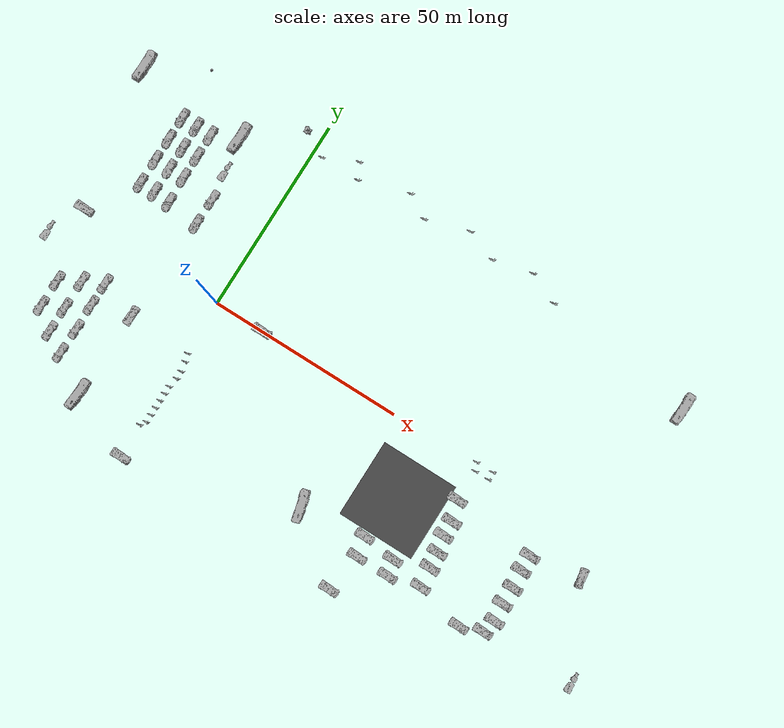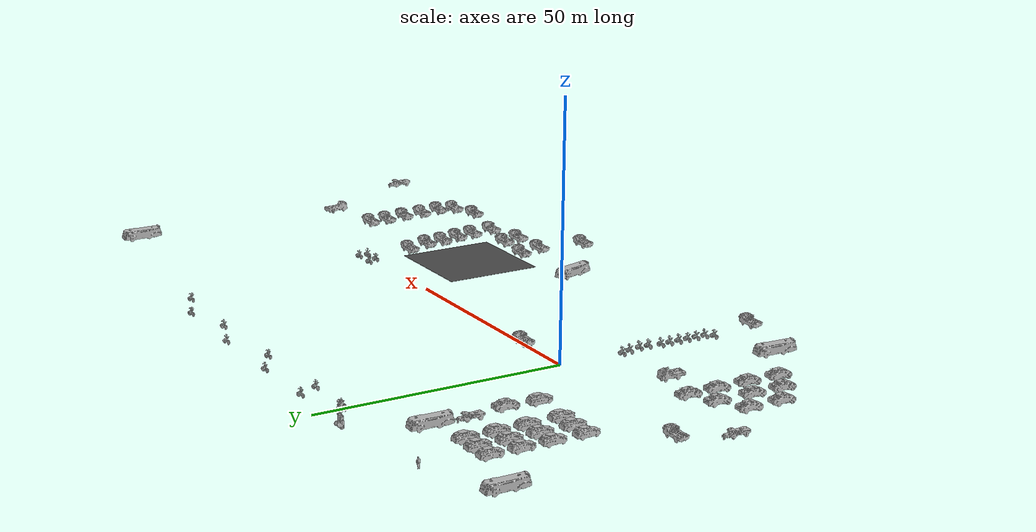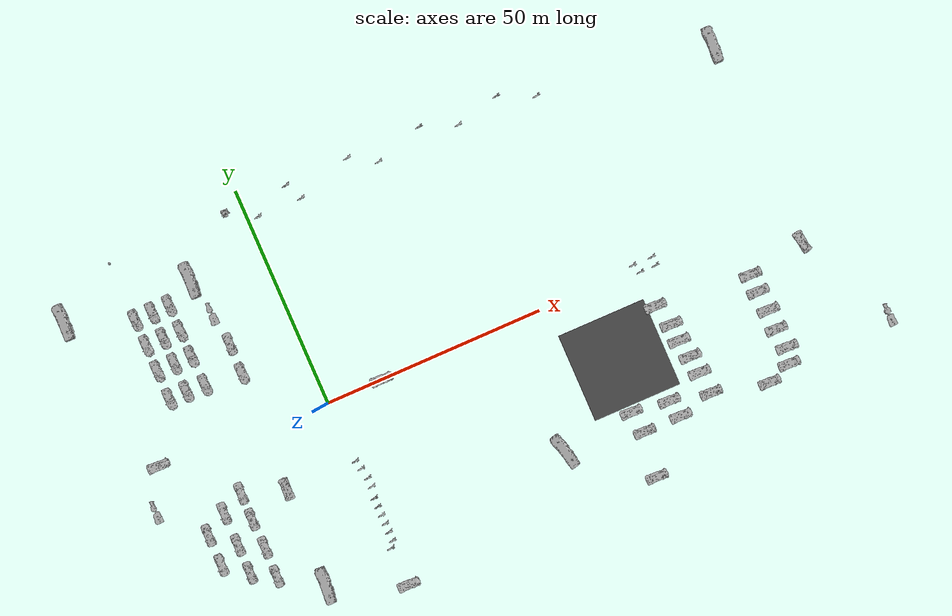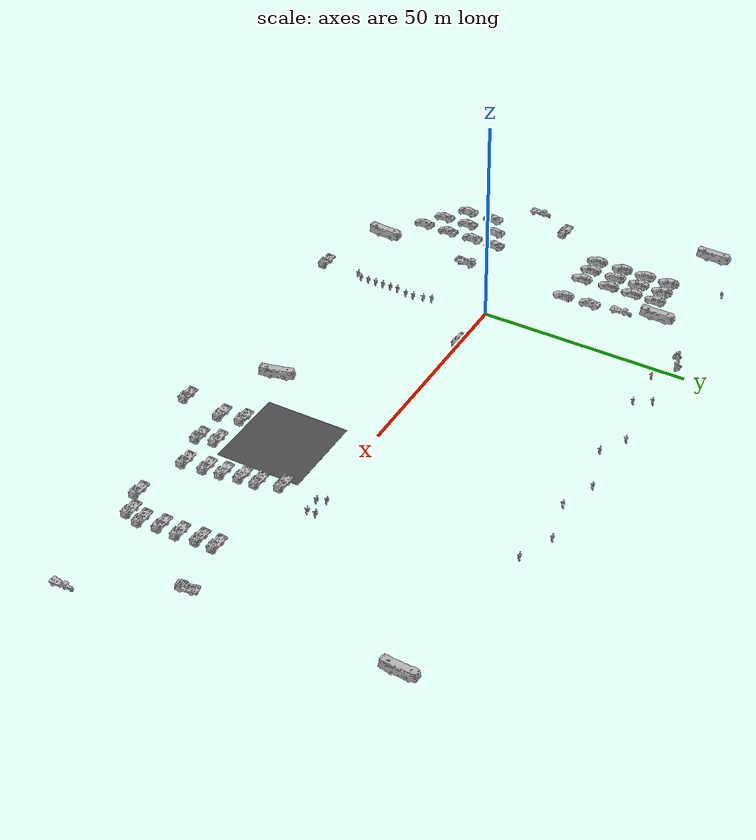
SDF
<sdf version="1.7">
 <world name="smoll_world">
  <scene>
   <grid>0</grid>
   <origin_visual>0</origin_visual>
   <ambient>0.85 0.85 0.85 1</ambient>
   <sky><clouds><speed>12</speed></clouds></sky>
   <background>0.35 0.35 0.35 1</background>
   <shadows>1</shadows>
  </scene>
  <physics name="default_physics" default="0" type="ode">
   <max_step_size>0.005</max_step_size>
   <real_time_factor>1</real_time_factor>
   <real_time_update_rate>200</real_time_update_rate>
  </physics>
  <light name="sun" type="directional">
   <pose>0 0 1000 0 -0 0</pose>
   <diffuse>0.8 0.8 0.8 1</diffuse>
   <specular>0.5 0.5 0.5 1</specular>
   <attenuation>
    <range>1000</range>
    <constant>0.9</constant>
    <linear>0.01</linear>
    <quadratic>0.001</quadratic>
   </attenuation>
   <direction>-0.5 0.1 -0.4</direction>
   <spot><inner_angle>0</inner_angle><outer_angle>0</outer_angle><falloff>0</falloff></spot>
  </light>
  <model name="ground_plane">
   <static>1</static>
   <link name="link">
    <collision name="collision">
     <geometry><plane><normal>0 0 1</normal><size>100 100</size></plane></geometry>
     <surface><friction><ode><mu>100</mu><mu2>50</mu2></ode></friction></surface>
    </collision>
   </link>
  </model>
  <model name="asphalt_plane_74">
   <static>1</static>
   <pose>61.581 -16.664 0 0 -0 0</pose>
   <link name="link">
    <visual name="visual">
     <geometry><box><size>20 20 0.05</size></box></geometry>
     <material>
      <script>
       <uri>model://asphalt_plane/materials/scripts</uri>
       <uri>model://asphalt_plane/materials/textures</uri>
       <name>vrc/asphalt</name>
      </script>
     </material>
    </visual>
   </link>
  </model>
  <gravity>0 0 -9.8</gravity>
  <magnetic_field>6e-06 2.3e-05 -4.2e-05</magnetic_field>
  <atmosphere type="adiabatic"/>
  <audio><device>default</device></audio>
  <spherical_coordinates>
   <surface_model>EARTH_WGS84</surface_model>
   <latitude_deg>0</latitude_deg>
   <longitude_deg>0</longitude_deg>
   <elevation>0</elevation>
   <heading_deg>0</heading_deg>
  </spherical_coordinates>
  <model name="kare-bus-2_clone">
   <model name="kare-bus">
    <static>1</static>
    <link name="link">
     <collision name="collision">
      <geometry><mesh><scale>8 8 8</scale><uri>model://kare-bus/meshes/kare-bus.obj</uri></mesh></geometry>
     </collision>
     <visual name="visual">
      <geometry><mesh><scale>8 8 8</scale><uri>model://kare-bus/meshes/kare-bus.obj</uri></mesh></geometry>
     </visual>
    </link>
    <pose>-3.3e-05 -0 -5e-06 1.57109 0.060055 1.57564</pose>
   </model>
   <static>0</static>
   <pose>-16.5988 36.2057 2.05341 0 0 1.55954</pose>
  </model>
  <model name="kare-bus-2_clone_0">
   <model name="kare-bus">
    <static>1</static>
    <link name="link">
     <collision name="collision">
      <geometry><mesh><scale>8 8 8</scale><uri>model://kare-bus/meshes/kare-bus.obj</uri></mesh></geometry>
     </collision>
     <visual name="visual">
      <geometry><mesh><scale>8 8 8</scale><uri>model://kare-bus/meshes/kare-bus.obj</uri></mesh></geometry>
     </visual>
    </link>
    <pose>-3.3e-05 -0 -5e-06 1.57109 0.060055 1.57564</pose>
   </model>
   <static>0</static>
   <pose>-45.2255 38.7045 2.05341 0 -0 1.56846</pose>
  </model>
  <model name="kare-bus-2_clone_2">
   <model name="kare-bus">
    <static>1</static>
    <link name="link">
     <collision name="collision">
      <geometry><mesh><scale>8 8 8</scale><uri>model://kare-bus/meshes/kare-bus.obj</uri></mesh></geometry>
     </collision>
     <visual name="visual">
      <geometry><mesh><scale>8 8 8</scale><uri>model://kare-bus/meshes/kare-bus.obj</uri></mesh></geometry>
     </visual>
    </link>
    <pose>-3.3e-05 -0 -5e-06 1.57109 0.060055 1.57564</pose>
   </model>
   <static>0</static>
   <pose>-16 -36 2.05341 0 0 1.51931</pose>
  </model>
  <model name="kare-bus-2_clone_3">
   <model name="kare-bus">
    <static>1</static>
    <link name="link">
     <collision name="collision">
      <geometry><mesh><scale>8 8 8</scale><uri>model://kare-bus/meshes/kare-bus.obj</uri></mesh></geometry>
     </collision>
     <visual name="visual">
      <geometry><mesh><scale>8 8 8</scale><uri>model://kare-bus/meshes/kare-bus.obj</uri></mesh></geometry>
     </visual>
    </link>
    <pose>-3.3e-05 -0 -5e-06 1.57109 0.060055 1.57564</pose>
   </model>
   <static>0</static>
   <pose>107.138 37.8184 2.05341 0 -0 1.5594</pose>
  </model>
  <model name="kare-man">
   <static>1</static>
   <link name="link">
    <collision name="collision">
     <geometry>
      <mesh><scale>2 2 2</scale><uri>/home/amadeus/model_editor_models/kare-man/meshes/kare-man.obj</uri></mesh>
     </geometry>
    </collision>
    <visual name="visual">
     <geometry>
      <mesh><scale>2 2 2</scale><uri>/home/amadeus/model_editor_models/kare-man/meshes/kare-man.obj</uri></mesh>
     </geometry>
    </visual>
   </link>
   <pose>-31.2235 46.3855 2.03741 1.57081 -0.001383 1.55971</pose>
  </model>
  <model name="bus56">
   <model name="kare-bus4">
    <model name="kare-bus-2">
     <model name="kare-bus">
      <static>1</static>
      <link name="link">
       <collision name="collision">
        <geometry>
         <mesh><scale>8 8 8</scale><uri>/home/amadeus/model_editor_models/kare-bus/meshes/kare-bus.obj</uri></mesh>
        </geometry>
       </collision>
       <visual name="visual">
        <geometry>
         <mesh><scale>8 8 8</scale><uri>/home/amadeus/model_editor_models/kare-bus/meshes/kare-bus.obj</uri></mesh>
        </geometry>
       </visual>
      </link>
      <pose>-3.3e-05 -0 -5e-06 1.57109 0.060055 1.57564</pose>
     </model>
     <static>0</static>
     <pose>4.1e-05 -4.9e-05 -0 0 -0 1.83082</pose>
    </model>
    <static>0</static>
    <pose>-4.2e-05 -5e-05 1.18266 0 -0 0</pose>
   </model>
   <static>0</static>
   <plugin name="model_move" filename="/home/amadeus/Downloads/dev_ws/src/articubot_one/worlds/build/libmodel_move.so"/>
   <pose>42.9302 -30.0519 5e-06 0 -0 5e-06</pose>
  </model>
  <model name="kare-lorry3">
   <model name="kare-lorry2">
    <model name="kare-emptylorry">
     <static>1</static>
     <link name="link">
      <collision name="collision">
       <geometry>
        <mesh>
         <scale>5 5 5</scale>
         <uri>/home/amadeus/model_editor_models/kare-emptylorry/meshes/kare-emptylorry.obj</uri>
        </mesh>
       </geometry>
      </collision>
      <visual name="visual">
       <geometry>
        <mesh>
         <scale>5 5 5</scale>
         <uri>/home/amadeus/model_editor_models/kare-emptylorry/meshes/kare-emptylorry.obj</uri>
        </mesh>
       </geometry>
      </visual>
     </link>
     <pose>-2.6e-05 -2.7e-05 -2e-06 1.55178 -0.050932 -1.58567</pose>
    </model>
    <static>0</static>
    <pose>2e-06 0 0.971266 0 -0 0</pose>
   </model>
   <static>1</static>
   <allow_auto_disable>0</allow_auto_disable>
   <plugin name="model_move" filename="/home/amadeus/Downloads/dev_ws/src/articubot_one/worlds/build/libmodel_move.so"/>
   <pose>12.7456 0.029316 0 0 0 0</pose>
  </model>
  <model name="kare-lorry3_clone">
   <model name="kare-lorry2">
    <model name="kare-emptylorry">
     <static>1</static>
     <link name="link">
      <collision name="collision">
       <geometry>
        <mesh>
         <scale>5 5 5</scale>
         <uri>/home/amadeus/model_editor_models/kare-emptylorry/meshes/kare-emptylorry.obj</uri>
        </mesh>
       </geometry>
      </collision>
      <visual name="visual">
       <geometry>
        <mesh>
         <scale>5 5 5</scale>
         <uri>/home/amadeus/model_editor_models/kare-emptylorry/meshes/kare-emptylorry.obj</uri>
        </mesh>
       </geometry>
      </visual>
     </link>
     <pose>-2.6e-05 -2.7e-05 -2e-06 1.55178 -0.050932 -1.58567</pose>
    </model>
    <static>0</static>
    <pose>2e-06 0 0.971266 0 -0 0</pose>
   </model>
   <static>1</static>
   <allow_auto_disable>0</allow_auto_disable>
   <plugin name="model_move" filename="/home/amadeus/Downloads/dev_ws/src/articubot_one/worlds/build/libmodel_move.so"/>
   <pose>-15.5223 -13.4936 -0 0 0 1.55929</pose>
  </model>
  <model name="kare-lorry3_clone_0">
   <model name="kare-lorry2">
    <model name="kare-emptylorry">
     <static>1</static>
     <link name="link">
      <collision name="collision">
       <geometry>
        <mesh>
         <scale>5 5 5</scale>
         <uri>/home/amadeus/model_editor_models/kare-emptylorry/meshes/kare-emptylorry.obj</uri>
        </mesh>
       </geometry>
      </collision>
      <visual name="visual">
       <geometry>
        <mesh>
         <scale>5 5 5</scale>
         <uri>/home/amadeus/model_editor_models/kare-emptylorry/meshes/kare-emptylorry.obj</uri>
        </mesh>
       </geometry>
      </visual>
     </link>
     <pose>-2.6e-05 -2.7e-05 -2e-06 1.55178 -0.050932 -1.58567</pose>
    </model>
    <static>0</static>
    <pose>2e-06 0 0.971266 0 -0 0</pose>
   </model>
   <static>1</static>
   <allow_auto_disable>0</allow_auto_disable>
   <plugin name="model_move" filename="/home/amadeus/Downloads/dev_ws/src/articubot_one/worlds/build/libmodel_move.so"/>
   <pose>0.478448 -43 0 0 0 0</pose>
  </model>
  <model name="kare-lorry3_clone_1">
   <model name="kare-lorry2">
    <model name="kare-emptylorry">
     <static>1</static>
     <link name="link">
      <collision name="collision">
       <geometry>
        <mesh>
         <scale>5 5 5</scale>
         <uri>/home/amadeus/model_editor_models/kare-emptylorry/meshes/kare-emptylorry.obj</uri>
        </mesh>
       </geometry>
      </collision>
      <visual name="visual">
       <geometry>
        <mesh>
         <scale>5 5 5</scale>
         <uri>/home/amadeus/model_editor_models/kare-emptylorry/meshes/kare-emptylorry.obj</uri>
        </mesh>
       </geometry>
      </visual>
     </link>
     <pose>-2.6e-05 -2.7e-05 -2e-06 1.55178 -0.050932 -1.58567</pose>
    </model>
    <static>0</static>
    <pose>2e-06 0 0.971266 0 -0 0</pose>
   </model>
   <static>1</static>
   <allow_auto_disable>0</allow_auto_disable>
   <plugin name="model_move" filename="/home/amadeus/Downloads/dev_ws/src/articubot_one/worlds/build/libmodel_move.so"/>
   <pose>59 -43 0 0 0 0</pose>
  </model>
  <model name="kare-lorry3_clone_2">
   <model name="kare-lorry2">
    <model name="kare-emptylorry">
     <static>1</static>
     <link name="link">
      <collision name="collision">
       <geometry>
        <mesh>
         <scale>5 5 5</scale>
         <uri>/home/amadeus/model_editor_models/kare-emptylorry/meshes/kare-emptylorry.obj</uri>
        </mesh>
       </geometry>
      </collision>
      <visual name="visual">
       <geometry>
        <mesh>
         <scale>5 5 5</scale>
         <uri>/home/amadeus/model_editor_models/kare-emptylorry/meshes/kare-emptylorry.obj</uri>
        </mesh>
       </geometry>
      </visual>
     </link>
     <pose>-2.6e-05 -2.7e-05 -2e-06 1.55178 -0.050932 -1.58567</pose>
    </model>
    <static>0</static>
    <pose>2e-06 0 0.971266 0 -0 0</pose>
   </model>
   <static>1</static>
   <allow_auto_disable>0</allow_auto_disable>
   <plugin name="model_move" filename="/home/amadeus/Downloads/dev_ws/src/articubot_one/worlds/build/libmodel_move.so"/>
   <pose>108 -9 -0 0 -0 -1.39707</pose>
  </model>
  <model name="kare-lorry3_clone_3">
   <model name="kare-lorry2">
    <model name="kare-emptylorry">
     <static>1</static>
     <link name="link">
      <collision name="collision">
       <geometry>
        <mesh>
         <scale>5 5 5</scale>
         <uri>/home/amadeus/model_editor_models/kare-emptylorry/meshes/kare-emptylorry.obj</uri>
        </mesh>
       </geometry>
      </collision>
      <visual name="visual">
       <geometry>
        <mesh>
         <scale>5 5 5</scale>
         <uri>/home/amadeus/model_editor_models/kare-emptylorry/meshes/kare-emptylorry.obj</uri>
        </mesh>
       </geometry>
      </visual>
     </link>
     <pose>-2.6e-05 -2.7e-05 -2e-06 1.55178 -0.050932 -1.58567</pose>
    </model>
    <static>0</static>
    <pose>2e-06 0 0.971266 0 -0 0</pose>
   </model>
   <static>1</static>
   <allow_auto_disable>0</allow_auto_disable>
   <plugin name="model_move" filename="/home/amadeus/Downloads/dev_ws/src/articubot_one/worlds/build/libmodel_move.so"/>
   <pose>73.4196 -9 0 0 0 0</pose>
  </model>
  <model name="kare-lorry3_clone_4">
   <model name="kare-lorry2">
    <model name="kare-emptylorry">
     <static>1</static>
     <link name="link">
      <collision name="collision">
       <geometry>
        <mesh>
         <scale>5 5 5</scale>
         <uri>/home/amadeus/model_editor_models/kare-emptylorry/meshes/kare-emptylorry.obj</uri>
        </mesh>
       </geometry>
      </collision>
      <visual name="visual">
       <geometry>
        <mesh>
         <scale>5 5 5</scale>
         <uri>/home/amadeus/model_editor_models/kare-emptylorry/meshes/kare-emptylorry.obj</uri>
        </mesh>
       </geometry>
      </visual>
     </link>
     <pose>-2.6e-05 -2.7e-05 -2e-06 1.55178 -0.050932 -1.58567</pose>
    </model>
    <static>0</static>
    <pose>2e-06 0 0.971266 0 -0 0</pose>
   </model>
   <static>1</static>
   <allow_auto_disable>0</allow_auto_disable>
   <plugin name="model_move" filename="/home/amadeus/Downloads/dev_ws/src/articubot_one/worlds/build/libmodel_move.so"/>
   <pose>75 -14 0 0 0 0</pose>
  </model>
  <model name="kare-lorry3_clone_5">
   <model name="kare-lorry2">
    <model name="kare-emptylorry">
     <static>1</static>
     <link name="link">
      <collision name="collision">
       <geometry>
        <mesh>
         <scale>5 5 5</scale>
         <uri>/home/amadeus/model_editor_models/kare-emptylorry/meshes/kare-emptylorry.obj</uri>
        </mesh>
       </geometry>
      </collision>
      <visual name="visual">
       <geometry>
        <mesh>
         <scale>5 5 5</scale>
         <uri>/home/amadeus/model_editor_models/kare-emptylorry/meshes/kare-emptylorry.obj</uri>
        </mesh>
       </geometry>
      </visual>
     </link>
     <pose>-2.6e-05 -2.7e-05 -2e-06 1.55178 -0.050932 -1.58567</pose>
    </model>
    <static>0</static>
    <pose>2e-06 0 0.971266 0 -0 0</pose>
   </model>
   <static>1</static>
   <allow_auto_disable>0</allow_auto_disable>
   <plugin name="model_move" filename="/home/amadeus/Downloads/dev_ws/src/articubot_one/worlds/build/libmodel_move.so"/>
   <pose>-38.9422 2.0981 0 0 -0 0</pose>
  </model>
  <model name="kare-lorry3_clone_3_clone">
   <model name="kare-lorry2">
    <model name="kare-emptylorry">
     <static>1</static>
     <link name="link">
      <collision name="collision">
       <geometry>
        <mesh>
         <scale>5 5 5</scale>
         <uri>/home/amadeus/model_editor_models/kare-emptylorry/meshes/kare-emptylorry.obj</uri>
        </mesh>
       </geometry>
      </collision>
      <visual name="visual">
       <geometry>
        <mesh>
         <scale>5 5 5</scale>
         <uri>/home/amadeus/model_editor_models/kare-emptylorry/meshes/kare-emptylorry.obj</uri>
        </mesh>
       </geometry>
      </visual>
     </link>
     <pose>-2.6e-05 -2.7e-05 -2e-06 1.55178 -0.050932 -1.58567</pose>
    </model>
    <static>0</static>
    <pose>2e-06 0 0.971266 0 -0 0</pose>
   </model>
   <static>1</static>
   <allow_auto_disable>0</allow_auto_disable>
   <plugin name="model_move" filename="/home/amadeus/Downloads/dev_ws/src/articubot_one/worlds/build/libmodel_move.so"/>
   <pose>75.1445 -17.8999 0 0 0 0</pose>
  </model>
  <model name="kare-lorry3_clone_3_clone_0">
   <model name="kare-lorry2">
    <model name="kare-emptylorry">
     <static>1</static>
     <link name="link">
      <collision name="collision">
       <geometry>
        <mesh>
         <scale>5 5 5</scale>
         <uri>/home/amadeus/model_editor_models/kare-emptylorry/meshes/kare-emptylorry.obj</uri>
        </mesh>
       </geometry>
      </collision>
      <visual name="visual">
       <geometry>
        <mesh>
         <scale>5 5 5</scale>
         <uri>/home/amadeus/model_editor_models/kare-emptylorry/meshes/kare-emptylorry.obj</uri>
        </mesh>
       </geometry>
      </visual>
     </link>
     <pose>-2.6e-05 -2.7e-05 -2e-06 1.55178 -0.050932 -1.58567</pose>
    </model>
    <static>0</static>
    <pose>2e-06 0 0.971266 0 -0 0</pose>
   </model>
   <static>1</static>
   <allow_auto_disable>0</allow_auto_disable>
   <plugin name="model_move" filename="/home/amadeus/Downloads/dev_ws/src/articubot_one/worlds/build/libmodel_move.so"/>
   <pose>76 -22 0 0 0 0</pose>
  </model>
  <model name="kare-lorry3_clone_3_clone_1">
   <model name="kare-lorry2">
    <model name="kare-emptylorry">
     <static>1</static>
     <link name="link">
      <collision name="collision">
       <geometry>
        <mesh>
         <scale>5 5 5</scale>
         <uri>/home/amadeus/model_editor_models/kare-emptylorry/meshes/kare-emptylorry.obj</uri>
        </mesh>
       </geometry>
      </collision>
      <visual name="visual">
       <geometry>
        <mesh>
         <scale>5 5 5</scale>
         <uri>/home/amadeus/model_editor_models/kare-emptylorry/meshes/kare-emptylorry.obj</uri>
        </mesh>
       </geometry>
      </visual>
     </link>
     <pose>-2.6e-05 -2.7e-05 -2e-06 1.55178 -0.050932 -1.58567</pose>
    </model>
    <static>0</static>
    <pose>2e-06 0 0.971266 0 -0 0</pose>
   </model>
   <static>1</static>
   <allow_auto_disable>0</allow_auto_disable>
   <plugin name="model_move" filename="/home/amadeus/Downloads/dev_ws/src/articubot_one/worlds/build/libmodel_move.so"/>
   <pose>76.4405 -26 0 0 0 0</pose>
  </model>
  <model name="kare-lorry3_clone_3_clone_2">
   <model name="kare-lorry2">
    <model name="kare-emptylorry">
     <static>1</static>
     <link name="link">
      <collision name="collision">
       <geometry>
        <mesh>
         <scale>5 5 5</scale>
         <uri>/home/amadeus/model_editor_models/kare-emptylorry/meshes/kare-emptylorry.obj</uri>
        </mesh>
       </geometry>
      </collision>
      <visual name="visual">
       <geometry>
        <mesh>
         <scale>5 5 5</scale>
         <uri>/home/amadeus/model_editor_models/kare-emptylorry/meshes/kare-emptylorry.obj</uri>
        </mesh>
       </geometry>
      </visual>
     </link>
     <pose>-2.6e-05 -2.7e-05 -2e-06 1.55178 -0.050932 -1.58567</pose>
    </model>
    <static>0</static>
    <pose>2e-06 0 0.971266 0 -0 0</pose>
   </model>
   <static>1</static>
   <allow_auto_disable>0</allow_auto_disable>
   <plugin name="model_move" filename="/home/amadeus/Downloads/dev_ws/src/articubot_one/worlds/build/libmodel_move.so"/>
   <pose>77 -31 0 0 0 0</pose>
  </model>
  <model name="kare-lorry3_clone_3_clone_3">
   <model name="kare-lorry2">
    <model name="kare-emptylorry">
     <static>1</static>
     <link name="link">
      <collision name="collision">
       <geometry>
        <mesh>
         <scale>5 5 5</scale>
         <uri>/home/amadeus/model_editor_models/kare-emptylorry/meshes/kare-emptylorry.obj</uri>
        </mesh>
       </geometry>
      </collision>
      <visual name="visual">
       <geometry>
        <mesh>
         <scale>5 5 5</scale>
         <uri>/home/amadeus/model_editor_models/kare-emptylorry/meshes/kare-emptylorry.obj</uri>
        </mesh>
       </geometry>
      </visual>
     </link>
     <pose>-2.6e-05 -2.7e-05 -2e-06 1.55178 -0.050932 -1.58567</pose>
    </model>
    <static>0</static>
    <pose>2e-06 0 0.971266 0 -0 0</pose>
   </model>
   <static>1</static>
   <allow_auto_disable>0</allow_auto_disable>
   <plugin name="model_move" filename="/home/amadeus/Downloads/dev_ws/src/articubot_one/worlds/build/libmodel_move.so"/>
   <pose>68 -29 0 0 0 0</pose>
  </model>
  <model name="kare-lorry3_clone_3_clone_4">
   <model name="kare-lorry2">
    <model name="kare-emptylorry">
     <static>1</static>
     <link name="link">
      <collision name="collision">
       <geometry>
        <mesh>
         <scale>5 5 5</scale>
         <uri>/home/amadeus/model_editor_models/kare-emptylorry/meshes/kare-emptylorry.obj</uri>
        </mesh>
       </geometry>
      </collision>
      <visual name="visual">
       <geometry>
        <mesh>
         <scale>5 5 5</scale>
         <uri>/home/amadeus/model_editor_models/kare-emptylorry/meshes/kare-emptylorry.obj</uri>
        </mesh>
       </geometry>
      </visual>
     </link>
     <pose>-2.6e-05 -2.7e-05 -2e-06 1.55178 -0.050932 -1.58567</pose>
    </model>
    <static>0</static>
    <pose>2e-06 0 0.971266 0 -0 0</pose>
   </model>
   <static>1</static>
   <allow_auto_disable>0</allow_auto_disable>
   <plugin name="model_move" filename="/home/amadeus/Downloads/dev_ws/src/articubot_one/worlds/build/libmodel_move.so"/>
   <pose>69 -33 0 0 0 0</pose>
  </model>
  <model name="kare-lorry3_clone_3_clone_5">
   <model name="kare-lorry2">
    <model name="kare-emptylorry">
     <static>1</static>
     <link name="link">
      <collision name="collision">
       <geometry>
        <mesh>
         <scale>5 5 5</scale>
         <uri>/home/amadeus/model_editor_models/kare-emptylorry/meshes/kare-emptylorry.obj</uri>
        </mesh>
       </geometry>
      </collision>
      <visual name="visual">
       <geometry>
        <mesh>
         <scale>5 5 5</scale>
         <uri>/home/amadeus/model_editor_models/kare-emptylorry/meshes/kare-emptylorry.obj</uri>
        </mesh>
       </geometry>
      </visual>
     </link>
     <pose>-2.6e-05 -2.7e-05 -2e-06 1.55178 -0.050932 -1.58567</pose>
    </model>
    <static>0</static>
    <pose>2e-06 0 0.971266 0 -0 0</pose>
   </model>
   <static>1</static>
   <allow_auto_disable>0</allow_auto_disable>
   <plugin name="model_move" filename="/home/amadeus/Downloads/dev_ws/src/articubot_one/worlds/build/libmodel_move.so"/>
   <pose>59.4904 -28 0 0 0 0</pose>
  </model>
  <model name="kare-lorry3_clone_3_clone_6">
   <model name="kare-lorry2">
    <model name="kare-emptylorry">
     <static>1</static>
     <link name="link">
      <collision name="collision">
       <geometry>
        <mesh>
         <scale>5 5 5</scale>
         <uri>/home/amadeus/model_editor_models/kare-emptylorry/meshes/kare-emptylorry.obj</uri>
        </mesh>
       </geometry>
      </collision>
      <visual name="visual">
       <geometry>
        <mesh>
         <scale>5 5 5</scale>
         <uri>/home/amadeus/model_editor_models/kare-emptylorry/meshes/kare-emptylorry.obj</uri>
        </mesh>
       </geometry>
      </visual>
     </link>
     <pose>-2.6e-05 -2.7e-05 -2e-06 1.55178 -0.050932 -1.58567</pose>
    </model>
    <static>0</static>
    <pose>2e-06 0 0.971266 0 -0 0</pose>
   </model>
   <static>1</static>
   <allow_auto_disable>0</allow_auto_disable>
   <plugin name="model_move" filename="/home/amadeus/Downloads/dev_ws/src/articubot_one/worlds/build/libmodel_move.so"/>
   <pose>60.4817 -33 0 0 0 0</pose>
  </model>
  <model name="kare-lorry3_clone_3_clone_7">
   <model name="kare-lorry2">
    <model name="kare-emptylorry">
     <static>1</static>
     <link name="link">
      <collision name="collision">
       <geometry>
        <mesh>
         <scale>5 5 5</scale>
         <uri>/home/amadeus/model_editor_models/kare-emptylorry/meshes/kare-emptylorry.obj</uri>
        </mesh>
       </geometry>
      </collision>
      <visual name="visual">
       <geometry>
        <mesh>
         <scale>5 5 5</scale>
         <uri>/home/amadeus/model_editor_models/kare-emptylorry/meshes/kare-emptylorry.obj</uri>
        </mesh>
       </geometry>
      </visual>
     </link>
     <pose>-2.6e-05 -2.7e-05 -2e-06 1.55178 -0.050932 -1.58567</pose>
    </model>
    <static>0</static>
    <pose>2e-06 0 0.971266 0 -0 0</pose>
   </model>
   <static>1</static>
   <allow_auto_disable>0</allow_auto_disable>
   <plugin name="model_move" filename="/home/amadeus/Downloads/dev_ws/src/articubot_one/worlds/build/libmodel_move.so"/>
   <pose>89.5026 -34 0 0 0 0</pose>
  </model>
  <model name="kare-lorry3_clone_3_clone_8">
   <model name="kare-lorry2">
    <model name="kare-emptylorry">
     <static>1</static>
     <link name="link">
      <collision name="collision">
       <geometry>
        <mesh>
         <scale>5 5 5</scale>
         <uri>/home/amadeus/model_editor_models/kare-emptylorry/meshes/kare-emptylorry.obj</uri>
        </mesh>
       </geometry>
      </collision>
      <visual name="visual">
       <geometry>
        <mesh>
         <scale>5 5 5</scale>
         <uri>/home/amadeus/model_editor_models/kare-emptylorry/meshes/kare-emptylorry.obj</uri>
        </mesh>
       </geometry>
      </visual>
     </link>
     <pose>-2.6e-05 -2.7e-05 -2e-06 1.55178 -0.050932 -1.58567</pose>
    </model>
    <static>0</static>
    <pose>2e-06 0 0.971266 0 -0 0</pose>
   </model>
   <static>1</static>
   <allow_auto_disable>0</allow_auto_disable>
   <plugin name="model_move" filename="/home/amadeus/Downloads/dev_ws/src/articubot_one/worlds/build/libmodel_move.so"/>
   <pose>95 -32 0 0 0 0</pose>
  </model>
  <model name="kare-lorry3_clone_3_clone_9">
   <model name="kare-lorry2">
    <model name="kare-emptylorry">
     <static>1</static>
     <link name="link">
      <collision name="collision">
       <geometry>
        <mesh>
         <scale>5 5 5</scale>
         <uri>/home/amadeus/model_editor_models/kare-emptylorry/meshes/kare-emptylorry.obj</uri>
        </mesh>
       </geometry>
      </collision>
      <visual name="visual">
       <geometry>
        <mesh>
         <scale>5 5 5</scale>
         <uri>/home/amadeus/model_editor_models/kare-emptylorry/meshes/kare-emptylorry.obj</uri>
        </mesh>
       </geometry>
      </visual>
     </link>
     <pose>-2.6e-05 -2.7e-05 -2e-06 1.55178 -0.050932 -1.58567</pose>
    </model>
    <static>0</static>
    <pose>2e-06 0 0.971266 0 -0 0</pose>
   </model>
   <static>1</static>
   <allow_auto_disable>0</allow_auto_disable>
   <plugin name="model_move" filename="/home/amadeus/Downloads/dev_ws/src/articubot_one/worlds/build/libmodel_move.so"/>
   <pose>96 -28.4952 0 0 0 0</pose>
  </model>
  <model name="kare-lorry3_clone_3_clone_10">
   <model name="kare-lorry2">
    <model name="kare-emptylorry">
     <static>1</static>
     <link name="link">
      <collision name="collision">
       <geometry>
        <mesh>
         <scale>5 5 5</scale>
         <uri>/home/amadeus/model_editor_models/kare-emptylorry/meshes/kare-emptylorry.obj</uri>
        </mesh>
       </geometry>
      </collision>
      <visual name="visual">
       <geometry>
        <mesh>
         <scale>5 5 5</scale>
         <uri>/home/amadeus/model_editor_models/kare-emptylorry/meshes/kare-emptylorry.obj</uri>
        </mesh>
       </geometry>
      </visual>
     </link>
     <pose>-2.6e-05 -2.7e-05 -2e-06 1.55178 -0.050932 -1.58567</pose>
    </model>
    <static>0</static>
    <pose>2e-06 0 0.971266 0 -0 0</pose>
   </model>
   <static>1</static>
   <allow_auto_disable>0</allow_auto_disable>
   <plugin name="model_move" filename="/home/amadeus/Downloads/dev_ws/src/articubot_one/worlds/build/libmodel_move.so"/>
   <pose>95.4546 -24 0 0 0 0</pose>
  </model>
  <model name="kare-lorry3_clone_3_clone_11">
   <model name="kare-lorry2">
    <model name="kare-emptylorry">
     <static>1</static>
     <link name="link">
      <collision name="collision">
       <geometry>
        <mesh>
         <scale>5 5 5</scale>
         <uri>/home/amadeus/model_editor_models/kare-emptylorry/meshes/kare-emptylorry.obj</uri>
        </mesh>
       </geometry>
      </collision>
      <visual name="visual">
       <geometry>
        <mesh>
         <scale>5 5 5</scale>
         <uri>/home/amadeus/model_editor_models/kare-emptylorry/meshes/kare-emptylorry.obj</uri>
        </mesh>
       </geometry>
      </visual>
     </link>
     <pose>-2.6e-05 -2.7e-05 -2e-06 1.55178 -0.050932 -1.58567</pose>
    </model>
    <static>0</static>
    <pose>2e-06 0 0.971266 0 -0 0</pose>
   </model>
   <static>1</static>
   <allow_auto_disable>0</allow_auto_disable>
   <plugin name="model_move" filename="/home/amadeus/Downloads/dev_ws/src/articubot_one/worlds/build/libmodel_move.so"/>
   <pose>95.4777 -19.5399 0 0 0 0</pose>
  </model>
  <model name="kare-lorry3_clone_3_clone_12">
   <model name="kare-lorry2">
    <model name="kare-emptylorry">
     <static>1</static>
     <link name="link">
      <collision name="collision">
       <geometry>
        <mesh>
         <scale>5 5 5</scale>
         <uri>/home/amadeus/model_editor_models/kare-emptylorry/meshes/kare-emptylorry.obj</uri>
        </mesh>
       </geometry>
      </collision>
      <visual name="visual">
       <geometry>
        <mesh>
         <scale>5 5 5</scale>
         <uri>/home/amadeus/model_editor_models/kare-emptylorry/meshes/kare-emptylorry.obj</uri>
        </mesh>
       </geometry>
      </visual>
     </link>
     <pose>-2.6e-05 -2.7e-05 -2e-06 1.55178 -0.050932 -1.58567</pose>
    </model>
    <static>0</static>
    <pose>2e-06 0 0.971266 0 -0 0</pose>
   </model>
   <static>1</static>
   <allow_auto_disable>0</allow_auto_disable>
   <plugin name="model_move" filename="/home/amadeus/Downloads/dev_ws/src/articubot_one/worlds/build/libmodel_move.so"/>
   <pose>95 -15 0 0 0 0</pose>
  </model>
  <model name="kare-lorry3_clone_3_clone_13">
   <model name="kare-lorry2">
    <model name="kare-emptylorry">
     <static>1</static>
     <link name="link">
      <collision name="collision">
       <geometry>
        <mesh>
         <scale>5 5 5</scale>
         <uri>/home/amadeus/model_editor_models/kare-emptylorry/meshes/kare-emptylorry.obj</uri>
        </mesh>
       </geometry>
      </collision>
      <visual name="visual">
       <geometry>
        <mesh>
         <scale>5 5 5</scale>
         <uri>/home/amadeus/model_editor_models/kare-emptylorry/meshes/kare-emptylorry.obj</uri>
        </mesh>
       </geometry>
      </visual>
     </link>
     <pose>-2.6e-05 -2.7e-05 -2e-06 1.55178 -0.050932 -1.58567</pose>
    </model>
    <static>0</static>
    <pose>2e-06 0 0.971266 0 -0 0</pose>
   </model>
   <static>1</static>
   <allow_auto_disable>0</allow_auto_disable>
   <plugin name="model_move" filename="/home/amadeus/Downloads/dev_ws/src/articubot_one/worlds/build/libmodel_move.so"/>
   <pose>95 -11 0 0 0 0</pose>
  </model>
  <model name="kare-cycle2">
   <model name="kare-cycle2">
    <model name="kare-cycle-2">
     <link name="link">
      <inertial>
       <mass>1</mass>
       <inertia><ixx>1</ixx><ixy>0</ixy><ixz>0</ixz><iyy>1</iyy><iyz>0</iyz><izz>1</izz></inertia>
      </inertial>
      <visual name="visual">
       <geometry><mesh><scale>2 2 2</scale><uri>model://kare-cycle/meshes/kare-cycle.obj</uri></mesh></geometry>
       <material><shader type="pixel"/></material>
      </visual>
      <collision name="collision">
       <geometry>
        <mesh><uri>/home/amadeus/model_editor_models/kare-cycle/meshes/kare-cycle.obj</uri><scale>2 2 2</scale></mesh>
       </geometry>
       <surface>
        <friction>
         <ode><mu>1</mu><mu2>1</mu2><fdir1>0 0 0</fdir1><slip1>0</slip1><slip2>0</slip2></ode>
         <torsional>
          <coefficient>1</coefficient>
          <patch_radius>0</patch_radius>
          <surface_radius>0</surface_radius>
          <use_patch_radius>1</use_patch_radius>
          <ode><slip>0</slip></ode>
         </torsional>
        </friction>
        <bounce><restitution_coefficient>0</restitution_coefficient><threshold>1e+06</threshold></bounce>
        <contact>
         <collide_without_contact>0</collide_without_contact>
         <collide_without_contact_bitmask>1</collide_without_contact_bitmask>
         <collide_bitmask>1</collide_bitmask>
         <ode>
          <soft_cfm>0</soft_cfm>
          <soft_erp>0.2</soft_erp>
          <kp>1e+13</kp>
          <kd>1</kd>
          <max_vel>0.01</max_vel>
          <min_depth>0</min_depth>
         </ode>
         <bullet>
          <split_impulse>1</split_impulse>
          <split_impulse_penetration_threshold>-0.01</split_impulse_penetration_threshold>
          <soft_cfm>0</soft_cfm>
          <soft_erp>0.2</soft_erp>
          <kp>1e+13</kp>
          <kd>1</kd>
         </bullet>
        </contact>
       </surface>
      </collision>
     </link>
     <static>1</static>
     <pose>4.5e-05 3e-06 6e-06 1.56443 -0.051805 1.69313</pose>
    </model>
    <static>0</static>
    <pose>9e-06 4e-06 -1e-06 0 -0 0</pose>
   </model>
   <static>0</static>
   <pose>2.25711 43.0319 0 0 0 0</pose>
  </model>
  <model name="kare-whitecar">
   <static>1</static>
   <link name="roof_link">
    <pose>0 0 3 0 -0 0</pose>
    <self_collide>1</self_collide>
    <enable_wind>1</enable_wind>
    <kinematic>1</kinematic>
   </link>
   <link name="link">
    <collision name="collision">
     <geometry>
      <mesh>
       <scale>5 5 5</scale>
       <uri>/home/amadeus/model_editor_models/kare-whitecar/meshes/kare-whitecar.obj</uri>
      </mesh>
     </geometry>
    </collision>
    <visual name="visual">
     <geometry>
      <mesh>
       <scale>5 5 5</scale>
       <uri>/home/amadeus/model_editor_models/kare-whitecar/meshes/kare-whitecar.obj</uri>
      </mesh>
     </geometry>
    </visual>
   </link>
   <pose>-14.2865 20.1093 1.09307 1.53975 -0 0</pose>
  </model>
  <model name="kare-redcar">
   <static>1</static>
   <link name="link">
    <collision name="collision">
     <geometry><mesh><scale>5 5 5</scale><uri>model://kare-redcar/meshes/kare-redcar.obj</uri></mesh></geometry>
    </collision>
    <visual name="visual">
     <geometry><mesh><scale>5 5 5</scale><uri>model://kare-redcar/meshes/kare-redcar.obj</uri></mesh></geometry>
    </visual>
   </link>
   <pose>-14.3919 13.2984 1.05721 1.56187 -0 0</pose>
  </model>
  <model name="kare-truck">
   <static>1</static>
   <link name="link">
    <collision name="collision">
     <geometry><mesh><scale>5 5 5</scale><uri>model://kare-truck/meshes/kare-truck.obj</uri></mesh></geometry>
    </collision>
    <visual name="visual">
     <geometry><mesh><scale>5 5 5</scale><uri>model://kare-truck/meshes/kare-truck.obj</uri></mesh></geometry>
    </visual>
   </link>
   <pose>-15.3088 27.6444 0.797515 1.55509 -0 0</pose>
  </model>
  <model name="kare-truck_clone">
   <static>1</static>
   <link name="link">
    <collision name="collision">
     <geometry><mesh><scale>5 5 5</scale><uri>model://kare-truck/meshes/kare-truck.obj</uri></mesh></geometry>
    </collision>
    <visual name="visual">
     <geometry><mesh><scale>5 5 5</scale><uri>model://kare-truck/meshes/kare-truck.obj</uri></mesh></geometry>
    </visual>
   </link>
   <pose>-4.02275 46.5958 0.931027 -3.08117 -0 0</pose>
  </model>
  <model name="kare-truck_clone_0">
   <static>1</static>
   <link name="link">
    <collision name="collision">
     <geometry><mesh><scale>5 5 5</scale><uri>model://kare-truck/meshes/kare-truck.obj</uri></mesh></geometry>
    </collision>
    <visual name="visual">
     <geometry><mesh><scale>5 5 5</scale><uri>model://kare-truck/meshes/kare-truck.obj</uri></mesh></geometry>
    </visual>
   </link>
   <pose>119 -31 0.931027 1.55509 -0 0</pose>
  </model>
  <model name="kare-truck_clone_1">
   <static>1</static>
   <link name="link">
    <collision name="collision">
     <geometry><mesh><scale>5 5 5</scale><uri>model://kare-truck/meshes/kare-truck.obj</uri></mesh></geometry>
    </collision>
    <visual name="visual">
     <geometry><mesh><scale>5 5 5</scale><uri>model://kare-truck/meshes/kare-truck.obj</uri></mesh></geometry>
    </visual>
   </link>
   <pose>-43.4966 -6.94322 0.931027 1.55509 -0 0</pose>
  </model>
  <model name="kare-redcar_clone">
   <static>1</static>
   <link name="link">
    <collision name="collision">
     <geometry><mesh><scale>5 5 5</scale><uri>model://kare-redcar/meshes/kare-redcar.obj</uri></mesh></geometry>
    </collision>
    <visual name="visual">
     <geometry><mesh><scale>5 5 5</scale><uri>model://kare-redcar/meshes/kare-redcar.obj</uri></mesh></geometry>
    </visual>
   </link>
   <pose>-22.7453 14.178 1.05721 1.56187 -0 0</pose>
  </model>
  <model name="kare-redcar_clone_0">
   <static>1</static>
   <link name="link">
    <collision name="collision">
     <geometry><mesh><scale>5 5 5</scale><uri>model://kare-redcar/meshes/kare-redcar.obj</uri></mesh></geometry>
    </collision>
    <visual name="visual">
     <geometry><mesh><scale>5 5 5</scale><uri>model://kare-redcar/meshes/kare-redcar.obj</uri></mesh></geometry>
    </visual>
   </link>
   <pose>-27 14.5179 1.05721 1.56187 -0 0</pose>
  </model>
  <model name="kare-redcar_clone_1">
   <static>1</static>
   <link name="link">
    <collision name="collision">
     <geometry><mesh><scale>5 5 5</scale><uri>model://kare-redcar/meshes/kare-redcar.obj</uri></mesh></geometry>
    </collision>
    <visual name="visual">
     <geometry><mesh><scale>5 5 5</scale><uri>model://kare-redcar/meshes/kare-redcar.obj</uri></mesh></geometry>
    </visual>
   </link>
   <pose>-31 14.4476 1.05721 1.56187 -0 0</pose>
  </model>
  <model name="kare-redcar_clone_2">
   <static>1</static>
   <link name="link">
    <collision name="collision">
     <geometry><mesh><scale>5 5 5</scale><uri>model://kare-redcar/meshes/kare-redcar.obj</uri></mesh></geometry>
    </collision>
    <visual name="visual">
     <geometry><mesh><scale>5 5 5</scale><uri>model://kare-redcar/meshes/kare-redcar.obj</uri></mesh></geometry>
    </visual>
   </link>
   <pose>-23 21 1.05721 1.56187 -0 0</pose>
  </model>
  <model name="kare-redcar_clone_3">
   <static>1</static>
   <link name="link">
    <collision name="collision">
     <geometry><mesh><scale>5 5 5</scale><uri>model://kare-redcar/meshes/kare-redcar.obj</uri></mesh></geometry>
    </collision>
    <visual name="visual">
     <geometry><mesh><scale>5 5 5</scale><uri>model://kare-redcar/meshes/kare-redcar.obj</uri></mesh></geometry>
    </visual>
   </link>
   <pose>-27 21 1.05721 1.56187 -0 0</pose>
  </model>
  <model name="kare-redcar_clone_4">
   <static>1</static>
   <link name="link">
    <collision name="collision">
     <geometry><mesh><scale>5 5 5</scale><uri>model://kare-redcar/meshes/kare-redcar.obj</uri></mesh></geometry>
    </collision>
    <visual name="visual">
     <geometry><mesh><scale>5 5 5</scale><uri>model://kare-redcar/meshes/kare-redcar.obj</uri></mesh></geometry>
    </visual>
   </link>
   <pose>-31 21 1.05721 1.56187 -0 0</pose>
  </model>
  <model name="kare-redcar_clone_5">
   <static>1</static>
   <link name="link">
    <collision name="collision">
     <geometry><mesh><scale>5 5 5</scale><uri>model://kare-redcar/meshes/kare-redcar.obj</uri></mesh></geometry>
    </collision>
    <visual name="visual">
     <geometry><mesh><scale>5 5 5</scale><uri>model://kare-redcar/meshes/kare-redcar.obj</uri></mesh></geometry>
    </visual>
   </link>
   <pose>-23 27 1.05721 1.56187 -0 0</pose>
  </model>
  <model name="kare-redcar_clone_6">
   <static>1</static>
   <link name="link">
    <collision name="collision">
     <geometry><mesh><scale>5 5 5</scale><uri>model://kare-redcar/meshes/kare-redcar.obj</uri></mesh></geometry>
    </collision>
    <visual name="visual">
     <geometry><mesh><scale>5 5 5</scale><uri>model://kare-redcar/meshes/kare-redcar.obj</uri></mesh></geometry>
    </visual>
   </link>
   <pose>-27 27 1.05721 1.56187 -0 0</pose>
  </model>
  <model name="kare-redcar_clone_7">
   <static>1</static>
   <link name="link">
    <collision name="collision">
     <geometry><mesh><scale>5 5 5</scale><uri>model://kare-redcar/meshes/kare-redcar.obj</uri></mesh></geometry>
    </collision>
    <visual name="visual">
     <geometry><mesh><scale>5 5 5</scale><uri>model://kare-redcar/meshes/kare-redcar.obj</uri></mesh></geometry>
    </visual>
   </link>
   <pose>-31 27 1.05721 1.56187 -0 0</pose>
  </model>
  <model name="kare-redcar_clone_8">
   <static>1</static>
   <link name="link">
    <collision name="collision">
     <geometry><mesh><scale>5 5 5</scale><uri>model://kare-redcar/meshes/kare-redcar.obj</uri></mesh></geometry>
    </collision>
    <visual name="visual">
     <geometry><mesh><scale>5 5 5</scale><uri>model://kare-redcar/meshes/kare-redcar.obj</uri></mesh></geometry>
    </visual>
   </link>
   <pose>-23 33 1.05721 1.56187 -0 0</pose>
  </model>
  <model name="kare-redcar_clone_9">
   <static>1</static>
   <link name="link">
    <collision name="collision">
     <geometry><mesh><scale>5 5 5</scale><uri>model://kare-redcar/meshes/kare-redcar.obj</uri></mesh></geometry>
    </collision>
    <visual name="visual">
     <geometry><mesh><scale>5 5 5</scale><uri>model://kare-redcar/meshes/kare-redcar.obj</uri></mesh></geometry>
    </visual>
   </link>
   <pose>-27 33 1.05721 1.56187 -0 0</pose>
  </model>
  <model name="kare-redcar_clone_10">
   <static>1</static>
   <link name="link">
    <collision name="collision">
     <geometry><mesh><scale>5 5 5</scale><uri>model://kare-redcar/meshes/kare-redcar.obj</uri></mesh></geometry>
    </collision>
    <visual name="visual">
     <geometry><mesh><scale>5 5 5</scale><uri>model://kare-redcar/meshes/kare-redcar.obj</uri></mesh></geometry>
    </visual>
   </link>
   <pose>-31 33 1.05721 1.56187 -0 0</pose>
  </model>
  <model name="kare-whitecar_clone">
   <static>1</static>
   <link name="roof_link">
    <pose>0 0 3 0 -0 0</pose>
    <self_collide>1</self_collide>
    <enable_wind>1</enable_wind>
    <kinematic>1</kinematic>
   </link>
   <link name="link">
    <collision name="collision">
     <geometry>
      <mesh>
       <scale>5 5 5</scale>
       <uri>/home/amadeus/model_editor_models/kare-whitecar/meshes/kare-whitecar.obj</uri>
      </mesh>
     </geometry>
    </collision>
    <visual name="visual">
     <geometry>
      <mesh>
       <scale>5 5 5</scale>
       <uri>/home/amadeus/model_editor_models/kare-whitecar/meshes/kare-whitecar.obj</uri>
      </mesh>
     </geometry>
    </visual>
   </link>
   <pose>-24.9422 -10.487 1.09307 1.53975 -0 0</pose>
  </model>
  <model name="kare-whitecar_clone_0">
   <static>1</static>
   <link name="roof_link">
    <pose>0 0 3 0 -0 0</pose>
    <self_collide>1</self_collide>
    <enable_wind>1</enable_wind>
    <kinematic>1</kinematic>
   </link>
   <link name="link">
    <collision name="collision">
     <geometry>
      <mesh>
       <scale>5 5 5</scale>
       <uri>/home/amadeus/model_editor_models/kare-whitecar/meshes/kare-whitecar.obj</uri>
      </mesh>
     </geometry>
    </collision>
    <visual name="visual">
     <geometry>
      <mesh>
       <scale>5 5 5</scale>
       <uri>/home/amadeus/model_editor_models/kare-whitecar/meshes/kare-whitecar.obj</uri>
      </mesh>
     </geometry>
    </visual>
   </link>
   <pose>-25 -16.589 1.09307 1.53975 -0 0</pose>
  </model>
  <model name="kare-whitecar_clone_1">
   <static>1</static>
   <link name="roof_link">
    <pose>0 0 3 0 -0 0</pose>
    <self_collide>1</self_collide>
    <enable_wind>1</enable_wind>
    <kinematic>1</kinematic>
   </link>
   <link name="link">
    <collision name="collision">
     <geometry>
      <mesh>
       <scale>5 5 5</scale>
       <uri>/home/amadeus/model_editor_models/kare-whitecar/meshes/kare-whitecar.obj</uri>
      </mesh>
     </geometry>
    </collision>
    <visual name="visual">
     <geometry>
      <mesh>
       <scale>5 5 5</scale>
       <uri>/home/amadeus/model_editor_models/kare-whitecar/meshes/kare-whitecar.obj</uri>
      </mesh>
     </geometry>
    </visual>
   </link>
   <pose>-24.8609 -23.2845 1.09307 1.53975 -0 0</pose>
  </model>
  <model name="kare-whitecar_clone_2">
   <static>1</static>
   <link name="roof_link">
    <pose>0 0 3 0 -0 0</pose>
    <self_collide>1</self_collide>
    <enable_wind>1</enable_wind>
    <kinematic>1</kinematic>
   </link>
   <link name="link">
    <collision name="collision">
     <geometry>
      <mesh>
       <scale>5 5 5</scale>
       <uri>/home/amadeus/model_editor_models/kare-whitecar/meshes/kare-whitecar.obj</uri>
      </mesh>
     </geometry>
    </collision>
    <visual name="visual">
     <geometry>
      <mesh>
       <scale>5 5 5</scale>
       <uri>/home/amadeus/model_editor_models/kare-whitecar/meshes/kare-whitecar.obj</uri>
      </mesh>
     </geometry>
    </visual>
   </link>
   <pose>-25 -30 1.09307 1.53975 -0 0</pose>
  </model>
  <model name="kare-whitecar_clone_3">
   <static>1</static>
   <link name="roof_link">
    <pose>0 0 3 0 -0 0</pose>
    <self_collide>1</self_collide>
    <enable_wind>1</enable_wind>
    <kinematic>1</kinematic>
   </link>
   <link name="link">
    <collision name="collision">
     <geometry>
      <mesh>
       <scale>5 5 5</scale>
       <uri>/home/amadeus/model_editor_models/kare-whitecar/meshes/kare-whitecar.obj</uri>
      </mesh>
     </geometry>
    </collision>
    <visual name="visual">
     <geometry>
      <mesh>
       <scale>5 5 5</scale>
       <uri>/home/amadeus/model_editor_models/kare-whitecar/meshes/kare-whitecar.obj</uri>
      </mesh>
     </geometry>
    </visual>
   </link>
   <pose>-30 -13 1.09307 1.53975 -0 0</pose>
  </model>
  <model name="kare-whitecar_clone_4">
   <static>1</static>
   <link name="roof_link">
    <pose>0 0 3 0 -0 0</pose>
    <self_collide>1</self_collide>
    <enable_wind>1</enable_wind>
    <kinematic>1</kinematic>
   </link>
   <link name="link">
    <collision name="collision">
     <geometry>
      <mesh>
       <scale>5 5 5</scale>
       <uri>/home/amadeus/model_editor_models/kare-whitecar/meshes/kare-whitecar.obj</uri>
      </mesh>
     </geometry>
    </collision>
    <visual name="visual">
     <geometry>
      <mesh>
       <scale>5 5 5</scale>
       <uri>/home/amadeus/model_editor_models/kare-whitecar/meshes/kare-whitecar.obj</uri>
      </mesh>
     </geometry>
    </visual>
   </link>
   <pose>-30 -20.4631 1.09307 1.53975 -0 0</pose>
  </model>
  <model name="kare-whitecar_clone_5">
   <static>1</static>
   <link name="roof_link">
    <pose>0 0 3 0 -0 0</pose>
    <self_collide>1</self_collide>
    <enable_wind>1</enable_wind>
    <kinematic>1</kinematic>
   </link>
   <link name="link">
    <collision name="collision">
     <geometry>
      <mesh>
       <scale>5 5 5</scale>
       <uri>/home/amadeus/model_editor_models/kare-whitecar/meshes/kare-whitecar.obj</uri>
      </mesh>
     </geometry>
    </collision>
    <visual name="visual">
     <geometry>
      <mesh>
       <scale>5 5 5</scale>
       <uri>/home/amadeus/model_editor_models/kare-whitecar/meshes/kare-whitecar.obj</uri>
      </mesh>
     </geometry>
    </visual>
   </link>
   <pose>-30 -27 1.09307 1.53975 -0 0</pose>
  </model>
  <model name="kare-whitecar_clone_6">
   <static>1</static>
   <link name="roof_link">
    <pose>0 0 3 0 -0 0</pose>
    <self_collide>1</self_collide>
    <enable_wind>1</enable_wind>
    <kinematic>1</kinematic>
   </link>
   <link name="link">
    <collision name="collision">
     <geometry>
      <mesh>
       <scale>5 5 5</scale>
       <uri>/home/amadeus/model_editor_models/kare-whitecar/meshes/kare-whitecar.obj</uri>
      </mesh>
     </geometry>
    </collision>
    <visual name="visual">
     <geometry>
      <mesh>
       <scale>5 5 5</scale>
       <uri>/home/amadeus/model_editor_models/kare-whitecar/meshes/kare-whitecar.obj</uri>
      </mesh>
     </geometry>
    </visual>
   </link>
   <pose>-35 -16 1.09307 1.53975 -0 0</pose>
  </model>
  <model name="kare-whitecar_clone_7">
   <static>1</static>
   <link name="roof_link">
    <pose>0 0 3 0 -0 0</pose>
    <self_collide>1</self_collide>
    <enable_wind>1</enable_wind>
    <kinematic>1</kinematic>
   </link>
   <link name="link">
    <collision name="collision">
     <geometry>
      <mesh>
       <scale>5 5 5</scale>
       <uri>/home/amadeus/model_editor_models/kare-whitecar/meshes/kare-whitecar.obj</uri>
      </mesh>
     </geometry>
    </collision>
    <visual name="visual">
     <geometry>
      <mesh>
       <scale>5 5 5</scale>
       <uri>/home/amadeus/model_editor_models/kare-whitecar/meshes/kare-whitecar.obj</uri>
      </mesh>
     </geometry>
    </visual>
   </link>
   <pose>-35 -23 1.09307 1.53975 -0 0</pose>
  </model>
  <model name="kare-cycle2_clone">
   <model name="kare-cycle2">
    <model name="kare-cycle-2">
     <link name="link">
      <inertial>
       <mass>1</mass>
       <inertia><ixx>1</ixx><ixy>0</ixy><ixz>0</ixz><iyy>1</iyy><iyz>0</iyz><izz>1</izz></inertia>
      </inertial>
      <visual name="visual">
       <geometry><mesh><scale>2 2 2</scale><uri>model://kare-cycle/meshes/kare-cycle.obj</uri></mesh></geometry>
       <material><shader type="pixel"/></material>
      </visual>
      <collision name="collision">
       <geometry>
        <mesh><uri>/home/amadeus/model_editor_models/kare-cycle/meshes/kare-cycle.obj</uri><scale>2 2 2</scale></mesh>
       </geometry>
       <surface>
        <friction>
         <ode><mu>1</mu><mu2>1</mu2><fdir1>0 0 0</fdir1><slip1>0</slip1><slip2>0</slip2></ode>
         <torsional>
          <coefficient>1</coefficient>
          <patch_radius>0</patch_radius>
          <surface_radius>0</surface_radius>
          <use_patch_radius>1</use_patch_radius>
          <ode><slip>0</slip></ode>
         </torsional>
        </friction>
        <bounce><restitution_coefficient>0</restitution_coefficient><threshold>1e+06</threshold></bounce>
        <contact>
         <collide_without_contact>0</collide_without_contact>
         <collide_without_contact_bitmask>1</collide_without_contact_bitmask>
         <collide_bitmask>1</collide_bitmask>
         <ode>
          <soft_cfm>0</soft_cfm>
          <soft_erp>0.2</soft_erp>
          <kp>1e+13</kp>
          <kd>1</kd>
          <max_vel>0.01</max_vel>
          <min_depth>0</min_depth>
         </ode>
         <bullet>
          <split_impulse>1</split_impulse>
          <split_impulse_penetration_threshold>-0.01</split_impulse_penetration_threshold>
          <soft_cfm>0</soft_cfm>
          <soft_erp>0.2</soft_erp>
          <kp>1e+13</kp>
          <kd>1</kd>
         </bullet>
        </contact>
       </surface>
      </collision>
     </link>
     <static>1</static>
     <pose>4.5e-05 3e-06 6e-06 1.56443 -0.051805 1.69313</pose>
    </model>
    <static>0</static>
    <pose>9e-06 4e-06 -1e-06 0 -0 0</pose>
   </model>
   <static>0</static>
   <pose>10.4568 46.8927 0 0 0 0</pose>
  </model>
  <model name="kare-cycle2_clone_0">
   <model name="kare-cycle2">
    <model name="kare-cycle-2">
     <link name="link">
      <inertial>
       <mass>1</mass>
       <inertia><ixx>1</ixx><ixy>0</ixy><ixz>0</ixz><iyy>1</iyy><iyz>0</iyz><izz>1</izz></inertia>
      </inertial>
      <visual name="visual">
       <geometry><mesh><scale>2 2 2</scale><uri>model://kare-cycle/meshes/kare-cycle.obj</uri></mesh></geometry>
       <material><shader type="pixel"/></material>
      </visual>
      <collision name="collision">
       <geometry>
        <mesh><uri>/home/amadeus/model_editor_models/kare-cycle/meshes/kare-cycle.obj</uri><scale>2 2 2</scale></mesh>
       </geometry>
       <surface>
        <friction>
         <ode><mu>1</mu><mu2>1</mu2><fdir1>0 0 0</fdir1><slip1>0</slip1><slip2>0</slip2></ode>
         <torsional>
          <coefficient>1</coefficient>
          <patch_radius>0</patch_radius>
          <surface_radius>0</surface_radius>
          <use_patch_radius>1</use_patch_radius>
          <ode><slip>0</slip></ode>
         </torsional>
        </friction>
        <bounce><restitution_coefficient>0</restitution_coefficient><threshold>1e+06</threshold></bounce>
        <contact>
         <collide_without_contact>0</collide_without_contact>
         <collide_without_contact_bitmask>1</collide_without_contact_bitmask>
         <collide_bitmask>1</collide_bitmask>
         <ode>
          <soft_cfm>0</soft_cfm>
          <soft_erp>0.2</soft_erp>
          <kp>1e+13</kp>
          <kd>1</kd>
          <max_vel>0.01</max_vel>
          <min_depth>0</min_depth>
         </ode>
         <bullet>
          <split_impulse>1</split_impulse>
          <split_impulse_penetration_threshold>-0.01</split_impulse_penetration_threshold>
          <soft_cfm>0</soft_cfm>
          <soft_erp>0.2</soft_erp>
          <kp>1e+13</kp>
          <kd>1</kd>
         </bullet>
        </contact>
       </surface>
      </collision>
     </link>
     <static>1</static>
     <pose>4.5e-05 3e-06 6e-06 1.56443 -0.051805 1.69313</pose>
    </model>
    <static>0</static>
    <pose>9e-06 4e-06 -1e-06 0 -0 0</pose>
   </model>
   <static>0</static>
   <pose>12.4072 43 0 0 0 0</pose>
  </model>
  <model name="kare-cycle2_clone_1">
   <model name="kare-cycle2">
    <model name="kare-cycle-2">
     <link name="link">
      <inertial>
       <mass>1</mass>
       <inertia><ixx>1</ixx><ixy>0</ixy><ixz>0</ixz><iyy>1</iyy><iyz>0</iyz><izz>1</izz></inertia>
      </inertial>
      <visual name="visual">
       <geometry><mesh><scale>2 2 2</scale><uri>model://kare-cycle/meshes/kare-cycle.obj</uri></mesh></geometry>
       <material><shader type="pixel"/></material>
      </visual>
      <collision name="collision">
       <geometry>
        <mesh><uri>/home/amadeus/model_editor_models/kare-cycle/meshes/kare-cycle.obj</uri><scale>2 2 2</scale></mesh>
       </geometry>
       <surface>
        <friction>
         <ode><mu>1</mu><mu2>1</mu2><fdir1>0 0 0</fdir1><slip1>0</slip1><slip2>0</slip2></ode>
         <torsional>
          <coefficient>1</coefficient>
          <patch_radius>0</patch_radius>
          <surface_radius>0</surface_radius>
          <use_patch_radius>1</use_patch_radius>
          <ode><slip>0</slip></ode>
         </torsional>
        </friction>
        <bounce><restitution_coefficient>0</restitution_coefficient><threshold>1e+06</threshold></bounce>
        <contact>
         <collide_without_contact>0</collide_without_contact>
         <collide_without_contact_bitmask>1</collide_without_contact_bitmask>
         <collide_bitmask>1</collide_bitmask>
         <ode>
          <soft_cfm>0</soft_cfm>
          <soft_erp>0.2</soft_erp>
          <kp>1e+13</kp>
          <kd>1</kd>
          <max_vel>0.01</max_vel>
          <min_depth>0</min_depth>
         </ode>
         <bullet>
          <split_impulse>1</split_impulse>
          <split_impulse_penetration_threshold>-0.01</split_impulse_penetration_threshold>
          <soft_cfm>0</soft_cfm>
          <soft_erp>0.2</soft_erp>
          <kp>1e+13</kp>
          <kd>1</kd>
         </bullet>
        </contact>
       </surface>
      </collision>
     </link>
     <static>1</static>
     <pose>4.5e-05 3e-06 6e-06 1.56443 -0.051805 1.69313</pose>
    </model>
    <static>0</static>
    <pose>9e-06 4e-06 -1e-06 0 -0 0</pose>
   </model>
   <static>0</static>
   <pose>25 47 0 0 0 0</pose>
  </model>
  <model name="kare-cycle2_clone_2">
   <model name="kare-cycle2">
    <model name="kare-cycle-2">
     <link name="link">
      <inertial>
       <mass>1</mass>
       <inertia><ixx>1</ixx><ixy>0</ixy><ixz>0</ixz><iyy>1</iyy><iyz>0</iyz><izz>1</izz></inertia>
      </inertial>
      <visual name="visual">
       <geometry><mesh><scale>2 2 2</scale><uri>model://kare-cycle/meshes/kare-cycle.obj</uri></mesh></geometry>
       <material><shader type="pixel"/></material>
      </visual>
      <collision name="collision">
       <geometry>
        <mesh><uri>/home/amadeus/model_editor_models/kare-cycle/meshes/kare-cycle.obj</uri><scale>2 2 2</scale></mesh>
       </geometry>
       <surface>
        <friction>
         <ode><mu>1</mu><mu2>1</mu2><fdir1>0 0 0</fdir1><slip1>0</slip1><slip2>0</slip2></ode>
         <torsional>
          <coefficient>1</coefficient>
          <patch_radius>0</patch_radius>
          <surface_radius>0</surface_radius>
          <use_patch_radius>1</use_patch_radius>
          <ode><slip>0</slip></ode>
         </torsional>
        </friction>
        <bounce><restitution_coefficient>0</restitution_coefficient><threshold>1e+06</threshold></bounce>
        <contact>
         <collide_without_contact>0</collide_without_contact>
         <collide_without_contact_bitmask>1</collide_without_contact_bitmask>
         <collide_bitmask>1</collide_bitmask>
         <ode>
          <soft_cfm>0</soft_cfm>
          <soft_erp>0.2</soft_erp>
          <kp>1e+13</kp>
          <kd>1</kd>
          <max_vel>0.01</max_vel>
          <min_depth>0</min_depth>
         </ode>
         <bullet>
          <split_impulse>1</split_impulse>
          <split_impulse_penetration_threshold>-0.01</split_impulse_penetration_threshold>
          <soft_cfm>0</soft_cfm>
          <soft_erp>0.2</soft_erp>
          <kp>1e+13</kp>
          <kd>1</kd>
         </bullet>
        </contact>
       </surface>
      </collision>
     </link>
     <static>1</static>
     <pose>4.5e-05 3e-06 6e-06 1.56443 -0.051805 1.69313</pose>
    </model>
    <static>0</static>
    <pose>9e-06 4e-06 -1e-06 0 -0 0</pose>
   </model>
   <static>0</static>
   <pose>31 43.5556 0 0 0 0</pose>
  </model>
  <model name="kare-cycle2_clone_3">
   <model name="kare-cycle2">
    <model name="kare-cycle-2">
     <link name="link">
      <inertial>
       <mass>1</mass>
       <inertia><ixx>1</ixx><ixy>0</ixy><ixz>0</ixz><iyy>1</iyy><iyz>0</iyz><izz>1</izz></inertia>
      </inertial>
      <visual name="visual">
       <geometry><mesh><scale>2 2 2</scale><uri>model://kare-cycle/meshes/kare-cycle.obj</uri></mesh></geometry>
       <material><shader type="pixel"/></material>
      </visual>
      <collision name="collision">
       <geometry>
        <mesh><uri>/home/amadeus/model_editor_models/kare-cycle/meshes/kare-cycle.obj</uri><scale>2 2 2</scale></mesh>
       </geometry>
       <surface>
        <friction>
         <ode><mu>1</mu><mu2>1</mu2><fdir1>0 0 0</fdir1><slip1>0</slip1><slip2>0</slip2></ode>
         <torsional>
          <coefficient>1</coefficient>
          <patch_radius>0</patch_radius>
          <surface_radius>0</surface_radius>
          <use_patch_radius>1</use_patch_radius>
          <ode><slip>0</slip></ode>
         </torsional>
        </friction>
        <bounce><restitution_coefficient>0</restitution_coefficient><threshold>1e+06</threshold></bounce>
        <contact>
         <collide_without_contact>0</collide_without_contact>
         <collide_without_contact_bitmask>1</collide_without_contact_bitmask>
         <collide_bitmask>1</collide_bitmask>
         <ode>
          <soft_cfm>0</soft_cfm>
          <soft_erp>0.2</soft_erp>
          <kp>1e+13</kp>
          <kd>1</kd>
          <max_vel>0.01</max_vel>
          <min_depth>0</min_depth>
         </ode>
         <bullet>
          <split_impulse>1</split_impulse>
          <split_impulse_penetration_threshold>-0.01</split_impulse_penetration_threshold>
          <soft_cfm>0</soft_cfm>
          <soft_erp>0.2</soft_erp>
          <kp>1e+13</kp>
          <kd>1</kd>
         </bullet>
        </contact>
       </surface>
      </collision>
     </link>
     <static>1</static>
     <pose>4.5e-05 3e-06 6e-06 1.56443 -0.051805 1.69313</pose>
    </model>
    <static>0</static>
    <pose>9e-06 4e-06 -1e-06 0 -0 0</pose>
   </model>
   <static>0</static>
   <pose>42 47 0 0 0 0</pose>
  </model>
  <model name="kare-cycle2_clone_4">
   <model name="kare-cycle2">
    <model name="kare-cycle-2">
     <link name="link">
      <inertial>
       <mass>1</mass>
       <inertia><ixx>1</ixx><ixy>0</ixy><ixz>0</ixz><iyy>1</iyy><iyz>0</iyz><izz>1</izz></inertia>
      </inertial>
      <visual name="visual">
       <geometry><mesh><scale>2 2 2</scale><uri>model://kare-cycle/meshes/kare-cycle.obj</uri></mesh></geometry>
       <material><shader type="pixel"/></material>
      </visual>
      <collision name="collision">
       <geometry>
        <mesh><uri>/home/amadeus/model_editor_models/kare-cycle/meshes/kare-cycle.obj</uri><scale>2 2 2</scale></mesh>
       </geometry>
       <surface>
        <friction>
         <ode><mu>1</mu><mu2>1</mu2><fdir1>0 0 0</fdir1><slip1>0</slip1><slip2>0</slip2></ode>
         <torsional>
          <coefficient>1</coefficient>
          <patch_radius>0</patch_radius>
          <surface_radius>0</surface_radius>
          <use_patch_radius>1</use_patch_radius>
          <ode><slip>0</slip></ode>
         </torsional>
        </friction>
        <bounce><restitution_coefficient>0</restitution_coefficient><threshold>1e+06</threshold></bounce>
        <contact>
         <collide_without_contact>0</collide_without_contact>
         <collide_without_contact_bitmask>1</collide_without_contact_bitmask>
         <collide_bitmask>1</collide_bitmask>
         <ode>
          <soft_cfm>0</soft_cfm>
          <soft_erp>0.2</soft_erp>
          <kp>1e+13</kp>
          <kd>1</kd>
          <max_vel>0.01</max_vel>
          <min_depth>0</min_depth>
         </ode>
         <bullet>
          <split_impulse>1</split_impulse>
          <split_impulse_penetration_threshold>-0.01</split_impulse_penetration_threshold>
          <soft_cfm>0</soft_cfm>
          <soft_erp>0.2</soft_erp>
          <kp>1e+13</kp>
          <kd>1</kd>
         </bullet>
        </contact>
       </surface>
      </collision>
     </link>
     <static>1</static>
     <pose>4.5e-05 3e-06 6e-06 1.56443 -0.051805 1.69313</pose>
    </model>
    <static>0</static>
    <pose>9e-06 4e-06 -1e-06 0 -0 0</pose>
   </model>
   <static>0</static>
   <pose>50 44 0 0 0 0</pose>
  </model>
  <model name="kare-cycle2_clone_5">
   <model name="kare-cycle2">
    <model name="kare-cycle-2">
     <link name="link">
      <inertial>
       <mass>1</mass>
       <inertia><ixx>1</ixx><ixy>0</ixy><ixz>0</ixz><iyy>1</iyy><iyz>0</iyz><izz>1</izz></inertia>
      </inertial>
      <visual name="visual">
       <geometry><mesh><scale>2 2 2</scale><uri>model://kare-cycle/meshes/kare-cycle.obj</uri></mesh></geometry>
       <material><shader type="pixel"/></material>
      </visual>
      <collision name="collision">
       <geometry>
        <mesh><uri>/home/amadeus/model_editor_models/kare-cycle/meshes/kare-cycle.obj</uri><scale>2 2 2</scale></mesh>
       </geometry>
       <surface>
        <friction>
         <ode><mu>1</mu><mu2>1</mu2><fdir1>0 0 0</fdir1><slip1>0</slip1><slip2>0</slip2></ode>
         <torsional>
          <coefficient>1</coefficient>
          <patch_radius>0</patch_radius>
          <surface_radius>0</surface_radius>
          <use_patch_radius>1</use_patch_radius>
          <ode><slip>0</slip></ode>
         </torsional>
        </friction>
        <bounce><restitution_coefficient>0</restitution_coefficient><threshold>1e+06</threshold></bounce>
        <contact>
         <collide_without_contact>0</collide_without_contact>
         <collide_without_contact_bitmask>1</collide_without_contact_bitmask>
         <collide_bitmask>1</collide_bitmask>
         <ode>
          <soft_cfm>0</soft_cfm>
          <soft_erp>0.2</soft_erp>
          <kp>1e+13</kp>
          <kd>1</kd>
          <max_vel>0.01</max_vel>
          <min_depth>0</min_depth>
         </ode>
         <bullet>
          <split_impulse>1</split_impulse>
          <split_impulse_penetration_threshold>-0.01</split_impulse_penetration_threshold>
          <soft_cfm>0</soft_cfm>
          <soft_erp>0.2</soft_erp>
          <kp>1e+13</kp>
          <kd>1</kd>
         </bullet>
        </contact>
       </surface>
      </collision>
     </link>
     <static>1</static>
     <pose>4.5e-05 3e-06 6e-06 1.56443 -0.051805 1.69313</pose>
    </model>
    <static>0</static>
    <pose>9e-06 4e-06 -1e-06 0 -0 0</pose>
   </model>
   <static>0</static>
   <pose>60 46.4117 0 0 0 0</pose>
  </model>
  <model name="kare-cycle2_clone_6">
   <model name="kare-cycle2">
    <model name="kare-cycle-2">
     <link name="link">
      <inertial>
       <mass>1</mass>
       <inertia><ixx>1</ixx><ixy>0</ixy><ixz>0</ixz><iyy>1</iyy><iyz>0</iyz><izz>1</izz></inertia>
      </inertial>
      <visual name="visual">
       <geometry><mesh><scale>2 2 2</scale><uri>model://kare-cycle/meshes/kare-cycle.obj</uri></mesh></geometry>
       <material><shader type="pixel"/></material>
      </visual>
      <collision name="collision">
       <geometry>
        <mesh><uri>/home/amadeus/model_editor_models/kare-cycle/meshes/kare-cycle.obj</uri><scale>2 2 2</scale></mesh>
       </geometry>
       <surface>
        <friction>
         <ode><mu>1</mu><mu2>1</mu2><fdir1>0 0 0</fdir1><slip1>0</slip1><slip2>0</slip2></ode>
         <torsional>
          <coefficient>1</coefficient>
          <patch_radius>0</patch_radius>
          <surface_radius>0</surface_radius>
          <use_patch_radius>1</use_patch_radius>
          <ode><slip>0</slip></ode>
         </torsional>
        </friction>
        <bounce><restitution_coefficient>0</restitution_coefficient><threshold>1e+06</threshold></bounce>
        <contact>
         <collide_without_contact>0</collide_without_contact>
         <collide_without_contact_bitmask>1</collide_without_contact_bitmask>
         <collide_bitmask>1</collide_bitmask>
         <ode>
          <soft_cfm>0</soft_cfm>
          <soft_erp>0.2</soft_erp>
          <kp>1e+13</kp>
          <kd>1</kd>
          <max_vel>0.01</max_vel>
          <min_depth>0</min_depth>
         </ode>
         <bullet>
          <split_impulse>1</split_impulse>
          <split_impulse_penetration_threshold>-0.01</split_impulse_penetration_threshold>
          <soft_cfm>0</soft_cfm>
          <soft_erp>0.2</soft_erp>
          <kp>1e+13</kp>
          <kd>1</kd>
         </bullet>
        </contact>
       </surface>
      </collision>
     </link>
     <static>1</static>
     <pose>4.5e-05 3e-06 6e-06 1.56443 -0.051805 1.69313</pose>
    </model>
    <static>0</static>
    <pose>9e-06 4e-06 -1e-06 0 -0 0</pose>
   </model>
   <static>0</static>
   <pose>68 43 0 0 0 0</pose>
  </model>
  <model name="kare-cycle2_clone_7">
   <model name="kare-cycle2">
    <model name="kare-cycle-2">
     <link name="link">
      <inertial>
       <mass>1</mass>
       <inertia><ixx>1</ixx><ixy>0</ixy><ixz>0</ixz><iyy>1</iyy><iyz>0</iyz><izz>1</izz></inertia>
      </inertial>
      <visual name="visual">
       <geometry><mesh><scale>2 2 2</scale><uri>model://kare-cycle/meshes/kare-cycle.obj</uri></mesh></geometry>
       <material><shader type="pixel"/></material>
      </visual>
      <collision name="collision">
       <geometry>
        <mesh><uri>/home/amadeus/model_editor_models/kare-cycle/meshes/kare-cycle.obj</uri><scale>2 2 2</scale></mesh>
       </geometry>
       <surface>
        <friction>
         <ode><mu>1</mu><mu2>1</mu2><fdir1>0 0 0</fdir1><slip1>0</slip1><slip2>0</slip2></ode>
         <torsional>
          <coefficient>1</coefficient>
          <patch_radius>0</patch_radius>
          <surface_radius>0</surface_radius>
          <use_patch_radius>1</use_patch_radius>
          <ode><slip>0</slip></ode>
         </torsional>
        </friction>
        <bounce><restitution_coefficient>0</restitution_coefficient><threshold>1e+06</threshold></bounce>
        <contact>
         <collide_without_contact>0</collide_without_contact>
         <collide_without_contact_bitmask>1</collide_without_contact_bitmask>
         <collide_bitmask>1</collide_bitmask>
         <ode>
          <soft_cfm>0</soft_cfm>
          <soft_erp>0.2</soft_erp>
          <kp>1e+13</kp>
          <kd>1</kd>
          <max_vel>0.01</max_vel>
          <min_depth>0</min_depth>
         </ode>
         <bullet>
          <split_impulse>1</split_impulse>
          <split_impulse_penetration_threshold>-0.01</split_impulse_penetration_threshold>
          <soft_cfm>0</soft_cfm>
          <soft_erp>0.2</soft_erp>
          <kp>1e+13</kp>
          <kd>1</kd>
         </bullet>
        </contact>
       </surface>
      </collision>
     </link>
     <static>1</static>
     <pose>4.5e-05 3e-06 6e-06 1.56443 -0.051805 1.69313</pose>
    </model>
    <static>0</static>
    <pose>9e-06 4e-06 -1e-06 0 -0 0</pose>
   </model>
   <static>0</static>
   <pose>77 1 0 0 0 0</pose>
  </model>
  <model name="kare-cycle2_clone_8">
   <model name="kare-cycle2">
    <model name="kare-cycle-2">
     <link name="link">
      <inertial>
       <mass>1</mass>
       <inertia><ixx>1</ixx><ixy>0</ixy><ixz>0</ixz><iyy>1</iyy><iyz>0</iyz><izz>1</izz></inertia>
      </inertial>
      <visual name="visual">
       <geometry><mesh><scale>2 2 2</scale><uri>model://kare-cycle/meshes/kare-cycle.obj</uri></mesh></geometry>
       <material><shader type="pixel"/></material>
      </visual>
      <collision name="collision">
       <geometry>
        <mesh><uri>/home/amadeus/model_editor_models/kare-cycle/meshes/kare-cycle.obj</uri><scale>2 2 2</scale></mesh>
       </geometry>
       <surface>
        <friction>
         <ode><mu>1</mu><mu2>1</mu2><fdir1>0 0 0</fdir1><slip1>0</slip1><slip2>0</slip2></ode>
         <torsional>
          <coefficient>1</coefficient>
          <patch_radius>0</patch_radius>
          <surface_radius>0</surface_radius>
          <use_patch_radius>1</use_patch_radius>
          <ode><slip>0</slip></ode>
         </torsional>
        </friction>
        <bounce><restitution_coefficient>0</restitution_coefficient><threshold>1e+06</threshold></bounce>
        <contact>
         <collide_without_contact>0</collide_without_contact>
         <collide_without_contact_bitmask>1</collide_without_contact_bitmask>
         <collide_bitmask>1</collide_bitmask>
         <ode>
          <soft_cfm>0</soft_cfm>
          <soft_erp>0.2</soft_erp>
          <kp>1e+13</kp>
          <kd>1</kd>
          <max_vel>0.01</max_vel>
          <min_depth>0</min_depth>
         </ode>
         <bullet>
          <split_impulse>1</split_impulse>
          <split_impulse_penetration_threshold>-0.01</split_impulse_penetration_threshold>
          <soft_cfm>0</soft_cfm>
          <soft_erp>0.2</soft_erp>
          <kp>1e+13</kp>
          <kd>1</kd>
         </bullet>
        </contact>
       </surface>
      </collision>
     </link>
     <static>1</static>
     <pose>4.5e-05 3e-06 6e-06 1.56443 -0.051805 1.69313</pose>
    </model>
    <static>0</static>
    <pose>9e-06 4e-06 -1e-06 0 -0 0</pose>
   </model>
   <static>0</static>
   <pose>72.5194 1 0 0 0 0</pose>
  </model>
  <model name="kare-cycle2_clone_9">
   <model name="kare-cycle2">
    <model name="kare-cycle-2">
     <link name="link">
      <inertial>
       <mass>1</mass>
       <inertia><ixx>1</ixx><ixy>0</ixy><ixz>0</ixz><iyy>1</iyy><iyz>0</iyz><izz>1</izz></inertia>
      </inertial>
      <visual name="visual">
       <geometry><mesh><scale>2 2 2</scale><uri>model://kare-cycle/meshes/kare-cycle.obj</uri></mesh></geometry>
       <material><shader type="pixel"/></material>
      </visual>
      <collision name="collision">
       <geometry>
        <mesh><uri>/home/amadeus/model_editor_models/kare-cycle/meshes/kare-cycle.obj</uri><scale>2 2 2</scale></mesh>
       </geometry>
       <surface>
        <friction>
         <ode><mu>1</mu><mu2>1</mu2><fdir1>0 0 0</fdir1><slip1>0</slip1><slip2>0</slip2></ode>
         <torsional>
          <coefficient>1</coefficient>
          <patch_radius>0</patch_radius>
          <surface_radius>0</surface_radius>
          <use_patch_radius>1</use_patch_radius>
          <ode><slip>0</slip></ode>
         </torsional>
        </friction>
        <bounce><restitution_coefficient>0</restitution_coefficient><threshold>1e+06</threshold></bounce>
        <contact>
         <collide_without_contact>0</collide_without_contact>
         <collide_without_contact_bitmask>1</collide_without_contact_bitmask>
         <collide_bitmask>1</collide_bitmask>
         <ode>
          <soft_cfm>0</soft_cfm>
          <soft_erp>0.2</soft_erp>
          <kp>1e+13</kp>
          <kd>1</kd>
          <max_vel>0.01</max_vel>
          <min_depth>0</min_depth>
         </ode>
         <bullet>
          <split_impulse>1</split_impulse>
          <split_impulse_penetration_threshold>-0.01</split_impulse_penetration_threshold>
          <soft_cfm>0</soft_cfm>
          <soft_erp>0.2</soft_erp>
          <kp>1e+13</kp>
          <kd>1</kd>
         </bullet>
        </contact>
       </surface>
      </collision>
     </link>
     <static>1</static>
     <pose>4.5e-05 3e-06 6e-06 1.56443 -0.051805 1.69313</pose>
    </model>
    <static>0</static>
    <pose>9e-06 4e-06 -1e-06 0 -0 0</pose>
   </model>
   <static>0</static>
   <pose>77 -1 0 0 0 0</pose>
  </model>
  <model name="kare-cycle2_clone_10">
   <model name="kare-cycle2">
    <model name="kare-cycle-2">
     <link name="link">
      <inertial>
       <mass>1</mass>
       <inertia><ixx>1</ixx><ixy>0</ixy><ixz>0</ixz><iyy>1</iyy><iyz>0</iyz><izz>1</izz></inertia>
      </inertial>
      <visual name="visual">
       <geometry><mesh><scale>2 2 2</scale><uri>model://kare-cycle/meshes/kare-cycle.obj</uri></mesh></geometry>
       <material><shader type="pixel"/></material>
      </visual>
      <collision name="collision">
       <geometry>
        <mesh><uri>/home/amadeus/model_editor_models/kare-cycle/meshes/kare-cycle.obj</uri><scale>2 2 2</scale></mesh>
       </geometry>
       <surface>
        <friction>
         <ode><mu>1</mu><mu2>1</mu2><fdir1>0 0 0</fdir1><slip1>0</slip1><slip2>0</slip2></ode>
         <torsional>
          <coefficient>1</coefficient>
          <patch_radius>0</patch_radius>
          <surface_radius>0</surface_radius>
          <use_patch_radius>1</use_patch_radius>
          <ode><slip>0</slip></ode>
         </torsional>
        </friction>
        <bounce><restitution_coefficient>0</restitution_coefficient><threshold>1e+06</threshold></bounce>
        <contact>
         <collide_without_contact>0</collide_without_contact>
         <collide_without_contact_bitmask>1</collide_without_contact_bitmask>
         <collide_bitmask>1</collide_bitmask>
         <ode>
          <soft_cfm>0</soft_cfm>
          <soft_erp>0.2</soft_erp>
          <kp>1e+13</kp>
          <kd>1</kd>
          <max_vel>0.01</max_vel>
          <min_depth>0</min_depth>
         </ode>
         <bullet>
          <split_impulse>1</split_impulse>
          <split_impulse_penetration_threshold>-0.01</split_impulse_penetration_threshold>
          <soft_cfm>0</soft_cfm>
          <soft_erp>0.2</soft_erp>
          <kp>1e+13</kp>
          <kd>1</kd>
         </bullet>
        </contact>
       </surface>
      </collision>
     </link>
     <static>1</static>
     <pose>4.5e-05 3e-06 6e-06 1.56443 -0.051805 1.69313</pose>
    </model>
    <static>0</static>
    <pose>9e-06 4e-06 -1e-06 0 -0 0</pose>
   </model>
   <static>0</static>
   <pose>73.4287 -1 0 0 0 0</pose>
  </model>
  <model name="kare-cycle2_clone_11">
   <model name="kare-cycle2">
    <model name="kare-cycle-2">
     <link name="link">
      <inertial>
       <mass>1</mass>
       <inertia><ixx>1</ixx><ixy>0</ixy><ixz>0</ixz><iyy>1</iyy><iyz>0</iyz><izz>1</izz></inertia>
      </inertial>
      <visual name="visual">
       <geometry><mesh><scale>2 2 2</scale><uri>model://kare-cycle/meshes/kare-cycle.obj</uri></mesh></geometry>
       <material><shader type="pixel"/></material>
      </visual>
      <collision name="collision">
       <geometry>
        <mesh><uri>/home/amadeus/model_editor_models/kare-cycle/meshes/kare-cycle.obj</uri><scale>2 2 2</scale></mesh>
       </geometry>
       <surface>
        <friction>
         <ode><mu>1</mu><mu2>1</mu2><fdir1>0 0 0</fdir1><slip1>0</slip1><slip2>0</slip2></ode>
         <torsional>
          <coefficient>1</coefficient>
          <patch_radius>0</patch_radius>
          <surface_radius>0</surface_radius>
          <use_patch_radius>1</use_patch_radius>
          <ode><slip>0</slip></ode>
         </torsional>
        </friction>
        <bounce><restitution_coefficient>0</restitution_coefficient><threshold>1e+06</threshold></bounce>
        <contact>
         <collide_without_contact>0</collide_without_contact>
         <collide_without_contact_bitmask>1</collide_without_contact_bitmask>
         <collide_bitmask>1</collide_bitmask>
         <ode>
          <soft_cfm>0</soft_cfm>
          <soft_erp>0.2</soft_erp>
          <kp>1e+13</kp>
          <kd>1</kd>
          <max_vel>0.01</max_vel>
          <min_depth>0</min_depth>
         </ode>
         <bullet>
          <split_impulse>1</split_impulse>
          <split_impulse_penetration_threshold>-0.01</split_impulse_penetration_threshold>
          <soft_cfm>0</soft_cfm>
          <soft_erp>0.2</soft_erp>
          <kp>1e+13</kp>
          <kd>1</kd>
         </bullet>
        </contact>
       </surface>
      </collision>
     </link>
     <static>1</static>
     <pose>4.5e-05 3e-06 6e-06 1.56443 -0.051805 1.69313</pose>
    </model>
    <static>0</static>
    <pose>9e-06 4e-06 -1e-06 0 -0 0</pose>
   </model>
   <static>0</static>
   <pose>0.462435 -14 0 0 0 0</pose>
  </model>
  <model name="kare-cycle2_clone_12">
   <model name="kare-cycle2">
    <model name="kare-cycle-2">
     <link name="link">
      <inertial>
       <mass>1</mass>
       <inertia><ixx>1</ixx><ixy>0</ixy><ixz>0</ixz><iyy>1</iyy><iyz>0</iyz><izz>1</izz></inertia>
      </inertial>
      <visual name="visual">
       <geometry><mesh><scale>2 2 2</scale><uri>model://kare-cycle/meshes/kare-cycle.obj</uri></mesh></geometry>
       <material><shader type="pixel"/></material>
      </visual>
      <collision name="collision">
       <geometry>
        <mesh><uri>/home/amadeus/model_editor_models/kare-cycle/meshes/kare-cycle.obj</uri><scale>2 2 2</scale></mesh>
       </geometry>
       <surface>
        <friction>
         <ode><mu>1</mu><mu2>1</mu2><fdir1>0 0 0</fdir1><slip1>0</slip1><slip2>0</slip2></ode>
         <torsional>
          <coefficient>1</coefficient>
          <patch_radius>0</patch_radius>
          <surface_radius>0</surface_radius>
          <use_patch_radius>1</use_patch_radius>
          <ode><slip>0</slip></ode>
         </torsional>
        </friction>
        <bounce><restitution_coefficient>0</restitution_coefficient><threshold>1e+06</threshold></bounce>
        <contact>
         <collide_without_contact>0</collide_without_contact>
         <collide_without_contact_bitmask>1</collide_without_contact_bitmask>
         <collide_bitmask>1</collide_bitmask>
         <ode>
          <soft_cfm>0</soft_cfm>
          <soft_erp>0.2</soft_erp>
          <kp>1e+13</kp>
          <kd>1</kd>
          <max_vel>0.01</max_vel>
          <min_depth>0</min_depth>
         </ode>
         <bullet>
          <split_impulse>1</split_impulse>
          <split_impulse_penetration_threshold>-0.01</split_impulse_penetration_threshold>
          <soft_cfm>0</soft_cfm>
          <soft_erp>0.2</soft_erp>
          <kp>1e+13</kp>
          <kd>1</kd>
         </bullet>
        </contact>
       </surface>
      </collision>
     </link>
     <static>1</static>
     <pose>4.5e-05 3e-06 6e-06 1.56443 -0.051805 1.69313</pose>
    </model>
    <static>0</static>
    <pose>9e-06 4e-06 -1e-06 0 -0 0</pose>
   </model>
   <static>0</static>
   <pose>1 -16 0 0 0 0</pose>
  </model>
  <model name="kare-cycle2_clone_13">
   <model name="kare-cycle2">
    <model name="kare-cycle-2">
     <link name="link">
      <inertial>
       <mass>1</mass>
       <inertia><ixx>1</ixx><ixy>0</ixy><ixz>0</ixz><iyy>1</iyy><iyz>0</iyz><izz>1</izz></inertia>
      </inertial>
      <visual name="visual">
       <geometry><mesh><scale>2 2 2</scale><uri>model://kare-cycle/meshes/kare-cycle.obj</uri></mesh></geometry>
       <material><shader type="pixel"/></material>
      </visual>
      <collision name="collision">
       <geometry>
        <mesh><uri>/home/amadeus/model_editor_models/kare-cycle/meshes/kare-cycle.obj</uri><scale>2 2 2</scale></mesh>
       </geometry>
       <surface>
        <friction>
         <ode><mu>1</mu><mu2>1</mu2><fdir1>0 0 0</fdir1><slip1>0</slip1><slip2>0</slip2></ode>
         <torsional>
          <coefficient>1</coefficient>
          <patch_radius>0</patch_radius>
          <surface_radius>0</surface_radius>
          <use_patch_radius>1</use_patch_radius>
          <ode><slip>0</slip></ode>
         </torsional>
        </friction>
        <bounce><restitution_coefficient>0</restitution_coefficient><threshold>1e+06</threshold></bounce>
        <contact>
         <collide_without_contact>0</collide_without_contact>
         <collide_without_contact_bitmask>1</collide_without_contact_bitmask>
         <collide_bitmask>1</collide_bitmask>
         <ode>
          <soft_cfm>0</soft_cfm>
          <soft_erp>0.2</soft_erp>
          <kp>1e+13</kp>
          <kd>1</kd>
          <max_vel>0.01</max_vel>
          <min_depth>0</min_depth>
         </ode>
         <bullet>
          <split_impulse>1</split_impulse>
          <split_impulse_penetration_threshold>-0.01</split_impulse_penetration_threshold>
          <soft_cfm>0</soft_cfm>
          <soft_erp>0.2</soft_erp>
          <kp>1e+13</kp>
          <kd>1</kd>
         </bullet>
        </contact>
       </surface>
      </collision>
     </link>
     <static>1</static>
     <pose>4.5e-05 3e-06 6e-06 1.56443 -0.051805 1.69313</pose>
    </model>
    <static>0</static>
    <pose>9e-06 4e-06 -1e-06 0 -0 0</pose>
   </model>
   <static>0</static>
   <pose>1.47409 -18.4446 0 0 0 0</pose>
  </model>
  <model name="kare-cycle2_clone_14">
   <model name="kare-cycle2">
    <model name="kare-cycle-2">
     <link name="link">
      <inertial>
       <mass>1</mass>
       <inertia><ixx>1</ixx><ixy>0</ixy><ixz>0</ixz><iyy>1</iyy><iyz>0</iyz><izz>1</izz></inertia>
      </inertial>
      <visual name="visual">
       <geometry><mesh><scale>2 2 2</scale><uri>model://kare-cycle/meshes/kare-cycle.obj</uri></mesh></geometry>
       <material><shader type="pixel"/></material>
      </visual>
      <collision name="collision">
       <geometry>
        <mesh><uri>/home/amadeus/model_editor_models/kare-cycle/meshes/kare-cycle.obj</uri><scale>2 2 2</scale></mesh>
       </geometry>
       <surface>
        <friction>
         <ode><mu>1</mu><mu2>1</mu2><fdir1>0 0 0</fdir1><slip1>0</slip1><slip2>0</slip2></ode>
         <torsional>
          <coefficient>1</coefficient>
          <patch_radius>0</patch_radius>
          <surface_radius>0</surface_radius>
          <use_patch_radius>1</use_patch_radius>
          <ode><slip>0</slip></ode>
         </torsional>
        </friction>
        <bounce><restitution_coefficient>0</restitution_coefficient><threshold>1e+06</threshold></bounce>
        <contact>
         <collide_without_contact>0</collide_without_contact>
         <collide_without_contact_bitmask>1</collide_without_contact_bitmask>
         <collide_bitmask>1</collide_bitmask>
         <ode>
          <soft_cfm>0</soft_cfm>
          <soft_erp>0.2</soft_erp>
          <kp>1e+13</kp>
          <kd>1</kd>
          <max_vel>0.01</max_vel>
          <min_depth>0</min_depth>
         </ode>
         <bullet>
          <split_impulse>1</split_impulse>
          <split_impulse_penetration_threshold>-0.01</split_impulse_penetration_threshold>
          <soft_cfm>0</soft_cfm>
          <soft_erp>0.2</soft_erp>
          <kp>1e+13</kp>
          <kd>1</kd>
         </bullet>
        </contact>
       </surface>
      </collision>
     </link>
     <static>1</static>
     <pose>4.5e-05 3e-06 6e-06 1.56443 -0.051805 1.69313</pose>
    </model>
    <static>0</static>
    <pose>9e-06 4e-06 -1e-06 0 -0 0</pose>
   </model>
   <static>0</static>
   <pose>1.49107 -20.4686 0 0 0 0</pose>
  </model>
  <model name="kare-cycle2_clone_15">
   <model name="kare-cycle2">
    <model name="kare-cycle-2">
     <link name="link">
      <inertial>
       <mass>1</mass>
       <inertia><ixx>1</ixx><ixy>0</ixy><ixz>0</ixz><iyy>1</iyy><iyz>0</iyz><izz>1</izz></inertia>
      </inertial>
      <visual name="visual">
       <geometry><mesh><scale>2 2 2</scale><uri>model://kare-cycle/meshes/kare-cycle.obj</uri></mesh></geometry>
       <material><shader type="pixel"/></material>
      </visual>
      <collision name="collision">
       <geometry>
        <mesh><uri>/home/amadeus/model_editor_models/kare-cycle/meshes/kare-cycle.obj</uri><scale>2 2 2</scale></mesh>
       </geometry>
       <surface>
        <friction>
         <ode><mu>1</mu><mu2>1</mu2><fdir1>0 0 0</fdir1><slip1>0</slip1><slip2>0</slip2></ode>
         <torsional>
          <coefficient>1</coefficient>
          <patch_radius>0</patch_radius>
          <surface_radius>0</surface_radius>
          <use_patch_radius>1</use_patch_radius>
          <ode><slip>0</slip></ode>
         </torsional>
        </friction>
        <bounce><restitution_coefficient>0</restitution_coefficient><threshold>1e+06</threshold></bounce>
        <contact>
         <collide_without_contact>0</collide_without_contact>
         <collide_without_contact_bitmask>1</collide_without_contact_bitmask>
         <collide_bitmask>1</collide_bitmask>
         <ode>
          <soft_cfm>0</soft_cfm>
          <soft_erp>0.2</soft_erp>
          <kp>1e+13</kp>
          <kd>1</kd>
          <max_vel>0.01</max_vel>
          <min_depth>0</min_depth>
         </ode>
         <bullet>
          <split_impulse>1</split_impulse>
          <split_impulse_penetration_threshold>-0.01</split_impulse_penetration_threshold>
          <soft_cfm>0</soft_cfm>
          <soft_erp>0.2</soft_erp>
          <kp>1e+13</kp>
          <kd>1</kd>
         </bullet>
        </contact>
       </surface>
      </collision>
     </link>
     <static>1</static>
     <pose>4.5e-05 3e-06 6e-06 1.56443 -0.051805 1.69313</pose>
    </model>
    <static>0</static>
    <pose>9e-06 4e-06 -1e-06 0 -0 0</pose>
   </model>
   <static>0</static>
   <pose>1 -23 0 0 0 0</pose>
  </model>
  <model name="kare-cycle2_clone_16">
   <model name="kare-cycle2">
    <model name="kare-cycle-2">
     <link name="link">
      <inertial>
       <mass>1</mass>
       <inertia><ixx>1</ixx><ixy>0</ixy><ixz>0</ixz><iyy>1</iyy><iyz>0</iyz><izz>1</izz></inertia>
      </inertial>
      <visual name="visual">
       <geometry><mesh><scale>2 2 2</scale><uri>model://kare-cycle/meshes/kare-cycle.obj</uri></mesh></geometry>
       <material><shader type="pixel"/></material>
      </visual>
      <collision name="collision">
       <geometry>
        <mesh><uri>/home/amadeus/model_editor_models/kare-cycle/meshes/kare-cycle.obj</uri><scale>2 2 2</scale></mesh>
       </geometry>
       <surface>
        <friction>
         <ode><mu>1</mu><mu2>1</mu2><fdir1>0 0 0</fdir1><slip1>0</slip1><slip2>0</slip2></ode>
         <torsional>
          <coefficient>1</coefficient>
          <patch_radius>0</patch_radius>
          <surface_radius>0</surface_radius>
          <use_patch_radius>1</use_patch_radius>
          <ode><slip>0</slip></ode>
         </torsional>
        </friction>
        <bounce><restitution_coefficient>0</restitution_coefficient><threshold>1e+06</threshold></bounce>
        <contact>
         <collide_without_contact>0</collide_without_contact>
         <collide_without_contact_bitmask>1</collide_without_contact_bitmask>
         <collide_bitmask>1</collide_bitmask>
         <ode>
          <soft_cfm>0</soft_cfm>
          <soft_erp>0.2</soft_erp>
          <kp>1e+13</kp>
          <kd>1</kd>
          <max_vel>0.01</max_vel>
          <min_depth>0</min_depth>
         </ode>
         <bullet>
          <split_impulse>1</split_impulse>
          <split_impulse_penetration_threshold>-0.01</split_impulse_penetration_threshold>
          <soft_cfm>0</soft_cfm>
          <soft_erp>0.2</soft_erp>
          <kp>1e+13</kp>
          <kd>1</kd>
         </bullet>
        </contact>
       </surface>
      </collision>
     </link>
     <static>1</static>
     <pose>4.5e-05 3e-06 6e-06 1.56443 -0.051805 1.69313</pose>
    </model>
    <static>0</static>
    <pose>9e-06 4e-06 -1e-06 0 -0 0</pose>
   </model>
   <static>0</static>
   <pose>1 -25 0 0 0 0</pose>
  </model>
  <model name="kare-cycle2_clone_17">
   <model name="kare-cycle2">
    <model name="kare-cycle-2">
     <link name="link">
      <inertial>
       <mass>1</mass>
       <inertia><ixx>1</ixx><ixy>0</ixy><ixz>0</ixz><iyy>1</iyy><iyz>0</iyz><izz>1</izz></inertia>
      </inertial>
      <visual name="visual">
       <geometry><mesh><scale>2 2 2</scale><uri>model://kare-cycle/meshes/kare-cycle.obj</uri></mesh></geometry>
       <material><shader type="pixel"/></material>
      </visual>
      <collision name="collision">
       <geometry>
        <mesh><uri>/home/amadeus/model_editor_models/kare-cycle/meshes/kare-cycle.obj</uri><scale>2 2 2</scale></mesh>
       </geometry>
       <surface>
        <friction>
         <ode><mu>1</mu><mu2>1</mu2><fdir1>0 0 0</fdir1><slip1>0</slip1><slip2>0</slip2></ode>
         <torsional>
          <coefficient>1</coefficient>
          <patch_radius>0</patch_radius>
          <surface_radius>0</surface_radius>
          <use_patch_radius>1</use_patch_radius>
          <ode><slip>0</slip></ode>
         </torsional>
        </friction>
        <bounce><restitution_coefficient>0</restitution_coefficient><threshold>1e+06</threshold></bounce>
        <contact>
         <collide_without_contact>0</collide_without_contact>
         <collide_without_contact_bitmask>1</collide_without_contact_bitmask>
         <collide_bitmask>1</collide_bitmask>
         <ode>
          <soft_cfm>0</soft_cfm>
          <soft_erp>0.2</soft_erp>
          <kp>1e+13</kp>
          <kd>1</kd>
          <max_vel>0.01</max_vel>
          <min_depth>0</min_depth>
         </ode>
         <bullet>
          <split_impulse>1</split_impulse>
          <split_impulse_penetration_threshold>-0.01</split_impulse_penetration_threshold>
          <soft_cfm>0</soft_cfm>
          <soft_erp>0.2</soft_erp>
          <kp>1e+13</kp>
          <kd>1</kd>
         </bullet>
        </contact>
       </surface>
      </collision>
     </link>
     <static>1</static>
     <pose>4.5e-05 3e-06 6e-06 1.56443 -0.051805 1.69313</pose>
    </model>
    <static>0</static>
    <pose>9e-06 4e-06 -1e-06 0 -0 0</pose>
   </model>
   <static>0</static>
   <pose>1 -27 0 0 0 0</pose>
  </model>
  <model name="kare-cycle2_clone_18">
   <model name="kare-cycle2">
    <model name="kare-cycle-2">
     <link name="link">
      <inertial>
       <mass>1</mass>
       <inertia><ixx>1</ixx><ixy>0</ixy><ixz>0</ixz><iyy>1</iyy><iyz>0</iyz><izz>1</izz></inertia>
      </inertial>
      <visual name="visual">
       <geometry><mesh><scale>2 2 2</scale><uri>model://kare-cycle/meshes/kare-cycle.obj</uri></mesh></geometry>
       <material><shader type="pixel"/></material>
      </visual>
      <collision name="collision">
       <geometry>
        <mesh><uri>/home/amadeus/model_editor_models/kare-cycle/meshes/kare-cycle.obj</uri><scale>2 2 2</scale></mesh>
       </geometry>
       <surface>
        <friction>
         <ode><mu>1</mu><mu2>1</mu2><fdir1>0 0 0</fdir1><slip1>0</slip1><slip2>0</slip2></ode>
         <torsional>
          <coefficient>1</coefficient>
          <patch_radius>0</patch_radius>
          <surface_radius>0</surface_radius>
          <use_patch_radius>1</use_patch_radius>
          <ode><slip>0</slip></ode>
         </torsional>
        </friction>
        <bounce><restitution_coefficient>0</restitution_coefficient><threshold>1e+06</threshold></bounce>
        <contact>
         <collide_without_contact>0</collide_without_contact>
         <collide_without_contact_bitmask>1</collide_without_contact_bitmask>
         <collide_bitmask>1</collide_bitmask>
         <ode>
          <soft_cfm>0</soft_cfm>
          <soft_erp>0.2</soft_erp>
          <kp>1e+13</kp>
          <kd>1</kd>
          <max_vel>0.01</max_vel>
          <min_depth>0</min_depth>
         </ode>
         <bullet>
          <split_impulse>1</split_impulse>
          <split_impulse_penetration_threshold>-0.01</split_impulse_penetration_threshold>
          <soft_cfm>0</soft_cfm>
          <soft_erp>0.2</soft_erp>
          <kp>1e+13</kp>
          <kd>1</kd>
         </bullet>
        </contact>
       </surface>
      </collision>
     </link>
     <static>1</static>
     <pose>4.5e-05 3e-06 6e-06 1.56443 -0.051805 1.69313</pose>
    </model>
    <static>0</static>
    <pose>9e-06 4e-06 -1e-06 0 -0 0</pose>
   </model>
   <static>0</static>
   <pose>1 -29 0 0 0 0</pose>
  </model>
  <model name="kare-cycle2_clone_19">
   <model name="kare-cycle2">
    <model name="kare-cycle-2">
     <link name="link">
      <inertial>
       <mass>1</mass>
       <inertia><ixx>1</ixx><ixy>0</ixy><ixz>0</ixz><iyy>1</iyy><iyz>0</iyz><izz>1</izz></inertia>
      </inertial>
      <visual name="visual">
       <geometry><mesh><scale>2 2 2</scale><uri>model://kare-cycle/meshes/kare-cycle.obj</uri></mesh></geometry>
       <material><shader type="pixel"/></material>
      </visual>
      <collision name="collision">
       <geometry>
        <mesh><uri>/home/amadeus/model_editor_models/kare-cycle/meshes/kare-cycle.obj</uri><scale>2 2 2</scale></mesh>
       </geometry>
       <surface>
        <friction>
         <ode><mu>1</mu><mu2>1</mu2><fdir1>0 0 0</fdir1><slip1>0</slip1><slip2>0</slip2></ode>
         <torsional>
          <coefficient>1</coefficient>
          <patch_radius>0</patch_radius>
          <surface_radius>0</surface_radius>
          <use_patch_radius>1</use_patch_radius>
          <ode><slip>0</slip></ode>
         </torsional>
        </friction>
        <bounce><restitution_coefficient>0</restitution_coefficient><threshold>1e+06</threshold></bounce>
        <contact>
         <collide_without_contact>0</collide_without_contact>
         <collide_without_contact_bitmask>1</collide_without_contact_bitmask>
         <collide_bitmask>1</collide_bitmask>
         <ode>
          <soft_cfm>0</soft_cfm>
          <soft_erp>0.2</soft_erp>
          <kp>1e+13</kp>
          <kd>1</kd>
          <max_vel>0.01</max_vel>
          <min_depth>0</min_depth>
         </ode>
         <bullet>
          <split_impulse>1</split_impulse>
          <split_impulse_penetration_threshold>-0.01</split_impulse_penetration_threshold>
          <soft_cfm>0</soft_cfm>
          <soft_erp>0.2</soft_erp>
          <kp>1e+13</kp>
          <kd>1</kd>
         </bullet>
        </contact>
       </surface>
      </collision>
     </link>
     <static>1</static>
     <pose>4.5e-05 3e-06 6e-06 1.56443 -0.051805 1.69313</pose>
    </model>
    <static>0</static>
    <pose>9e-06 4e-06 -1e-06 0 -0 0</pose>
   </model>
   <static>0</static>
   <pose>1 -31 0 0 0 0</pose>
  </model>
  <model name="kare-cycle2_clone_20">
   <model name="kare-cycle2">
    <model name="kare-cycle-2">
     <link name="link">
      <inertial>
       <mass>1</mass>
       <inertia><ixx>1</ixx><ixy>0</ixy><ixz>0</ixz><iyy>1</iyy><iyz>0</iyz><izz>1</izz></inertia>
      </inertial>
      <visual name="visual">
       <geometry><mesh><scale>2 2 2</scale><uri>model://kare-cycle/meshes/kare-cycle.obj</uri></mesh></geometry>
       <material><shader type="pixel"/></material>
      </visual>
      <collision name="collision">
       <geometry>
        <mesh><uri>/home/amadeus/model_editor_models/kare-cycle/meshes/kare-cycle.obj</uri><scale>2 2 2</scale></mesh>
       </geometry>
       <surface>
        <friction>
         <ode><mu>1</mu><mu2>1</mu2><fdir1>0 0 0</fdir1><slip1>0</slip1><slip2>0</slip2></ode>
         <torsional>
          <coefficient>1</coefficient>
          <patch_radius>0</patch_radius>
          <surface_radius>0</surface_radius>
          <use_patch_radius>1</use_patch_radius>
          <ode><slip>0</slip></ode>
         </torsional>
        </friction>
        <bounce><restitution_coefficient>0</restitution_coefficient><threshold>1e+06</threshold></bounce>
        <contact>
         <collide_without_contact>0</collide_without_contact>
         <collide_without_contact_bitmask>1</collide_without_contact_bitmask>
         <collide_bitmask>1</collide_bitmask>
         <ode>
          <soft_cfm>0</soft_cfm>
          <soft_erp>0.2</soft_erp>
          <kp>1e+13</kp>
          <kd>1</kd>
          <max_vel>0.01</max_vel>
          <min_depth>0</min_depth>
         </ode>
         <bullet>
          <split_impulse>1</split_impulse>
          <split_impulse_penetration_threshold>-0.01</split_impulse_penetration_threshold>
          <soft_cfm>0</soft_cfm>
          <soft_erp>0.2</soft_erp>
          <kp>1e+13</kp>
          <kd>1</kd>
         </bullet>
        </contact>
       </surface>
      </collision>
     </link>
     <static>1</static>
     <pose>4.5e-05 3e-06 6e-06 1.56443 -0.051805 1.69313</pose>
    </model>
    <static>0</static>
    <pose>9e-06 4e-06 -1e-06 0 -0 0</pose>
   </model>
   <static>0</static>
   <pose>1 -33 0 0 0 0</pose>
  </model>
  <model name="kare-cycle2_clone_21">
   <model name="kare-cycle2">
    <model name="kare-cycle-2">
     <link name="link">
      <inertial>
       <mass>1</mass>
       <inertia><ixx>1</ixx><ixy>0</ixy><ixz>0</ixz><iyy>1</iyy><iyz>0</iyz><izz>1</izz></inertia>
      </inertial>
      <visual name="visual">
       <geometry><mesh><scale>2 2 2</scale><uri>model://kare-cycle/meshes/kare-cycle.obj</uri></mesh></geometry>
       <material><shader type="pixel"/></material>
      </visual>
      <collision name="collision">
       <geometry>
        <mesh><uri>/home/amadeus/model_editor_models/kare-cycle/meshes/kare-cycle.obj</uri><scale>2 2 2</scale></mesh>
       </geometry>
       <surface>
        <friction>
         <ode><mu>1</mu><mu2>1</mu2><fdir1>0 0 0</fdir1><slip1>0</slip1><slip2>0</slip2></ode>
         <torsional>
          <coefficient>1</coefficient>
          <patch_radius>0</patch_radius>
          <surface_radius>0</surface_radius>
          <use_patch_radius>1</use_patch_radius>
          <ode><slip>0</slip></ode>
         </torsional>
        </friction>
        <bounce><restitution_coefficient>0</restitution_coefficient><threshold>1e+06</threshold></bounce>
        <contact>
         <collide_without_contact>0</collide_without_contact>
         <collide_without_contact_bitmask>1</collide_without_contact_bitmask>
         <collide_bitmask>1</collide_bitmask>
         <ode>
          <soft_cfm>0</soft_cfm>
          <soft_erp>0.2</soft_erp>
          <kp>1e+13</kp>
          <kd>1</kd>
          <max_vel>0.01</max_vel>
          <min_depth>0</min_depth>
         </ode>
         <bullet>
          <split_impulse>1</split_impulse>
          <split_impulse_penetration_threshold>-0.01</split_impulse_penetration_threshold>
          <soft_cfm>0</soft_cfm>
          <soft_erp>0.2</soft_erp>
          <kp>1e+13</kp>
          <kd>1</kd>
         </bullet>
        </contact>
       </surface>
      </collision>
     </link>
     <static>1</static>
     <pose>4.5e-05 3e-06 6e-06 1.56443 -0.051805 1.69313</pose>
    </model>
    <static>0</static>
    <pose>9e-06 4e-06 -1e-06 0 -0 0</pose>
   </model>
   <static>0</static>
   <pose>0 -34.4178 0 0 0 0</pose>
  </model>
 </world>
</sdf>
